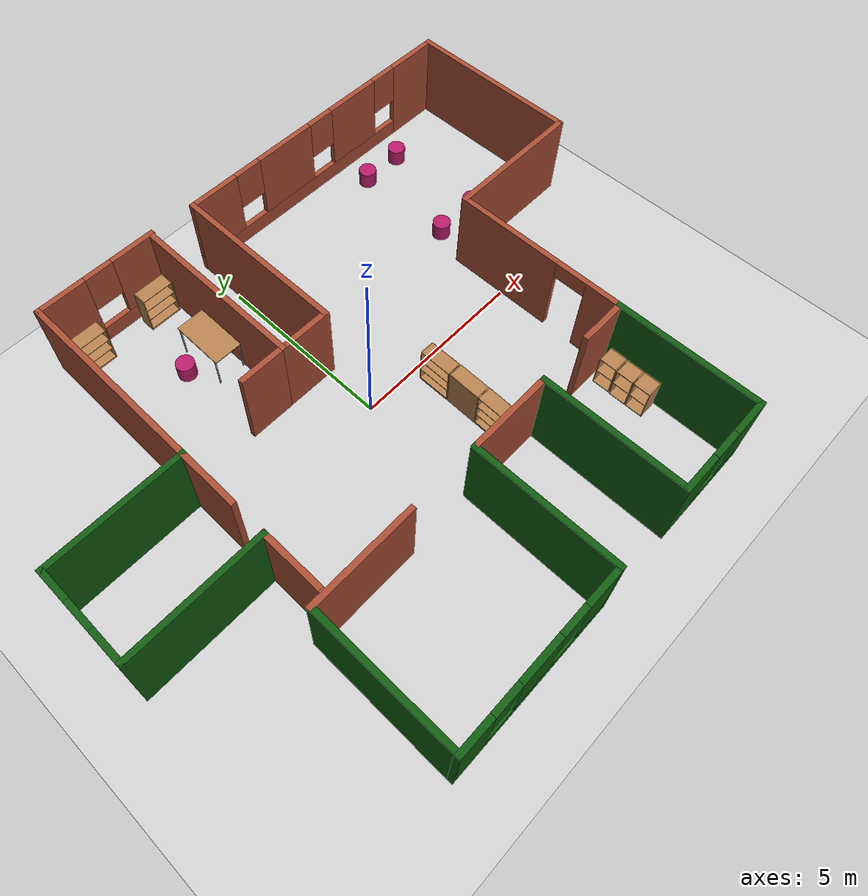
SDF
<sdf version="1.6">
 <world name="default">
  <plugin name="welcome" filename="libwelcome.so"/>
  <light name="sun" type="directional">
   <pose>0 0 10 0 -0 0</pose>
   <diffuse>0.8 0.8 0.8 1</diffuse>
   <specular>0.2 0.2 0.2 1</specular>
   <attenuation>
    <range>1000</range>
    <constant>0.9</constant>
    <linear>0.01</linear>
    <quadratic>0.001</quadratic>
   </attenuation>
   <direction>-0.5 0.1 -0.9</direction>
  </light>
  <model name="ground_plane">
   <static>1</static>
   <link name="link">
    <collision name="collision">
     <geometry><plane><normal>0 0 1</normal><size>100 100</size></plane></geometry>
     <surface>
      <contact><collide_bitmask>65535</collide_bitmask></contact>
      <friction><ode><mu>100</mu><mu2>50</mu2></ode></friction>
     </surface>
    </collision>
    <visual name="visual">
     <cast_shadows>0</cast_shadows>
     <geometry><plane><normal>0 0 1</normal><size>100 100</size></plane></geometry>
     <material>
      <script><uri>file://media/materials/scripts/gazebo.material</uri><name>Gazebo/Grey</name></script>
     </material>
    </visual>
   </link>
  </model>
  <gravity>0 0 -9.8</gravity>
  <magnetic_field>6e-06 2.3e-05 -4.2e-05</magnetic_field>
  <atmosphere type="adiabatic"/>
  <physics name="default_physics" default="0" type="ode">
   <max_step_size>0.001</max_step_size>
   <real_time_factor>1</real_time_factor>
   <real_time_update_rate>1000</real_time_update_rate>
  </physics>
  <scene><ambient>0.4 0.4 0.4 1</ambient><background>0.7 0.7 0.7 1</background><shadows>1</shadows></scene>
  <audio><device>default</device></audio>
  <spherical_coordinates>
   <surface_model>EARTH_WGS84</surface_model>
   <latitude_deg>0</latitude_deg>
   <longitude_deg>0</longitude_deg>
   <elevation>0</elevation>
   <heading_deg>0</heading_deg>
  </spherical_coordinates>
  <model name="apartment">
   <link name="Wall_0">
    <pose>-2.91418 -6.79442 0 0 -0 0</pose>
    <visual name="Wall_0_Visual_0">
     <pose>-1.99956 0 1.25 0 -0 0</pose>
     <geometry><box><size>1.00087 0.15 2.5</size></box></geometry>
     <material>
      <script><uri>file://media/materials/scripts/gazebo.material</uri><name>Gazebo/Grey</name></script>
      <ambient>0.0627451 0.352941 0.0627451 1</ambient>
     </material>
     <meta><layer>0</layer></meta>
    </visual>
    <visual name="Wall_0_Visual_1">
     <pose>0.500436 0 0.25 0 -0 0</pose>
     <geometry><box><size>3.99913 0.15 0.5</size></box></geometry>
     <material>
      <script><uri>file://media/materials/scripts/gazebo.material</uri><name>Gazebo/Grey</name></script>
      <ambient>0.0627451 0.352941 0.0627451 1</ambient>
     </material>
     <meta><layer>0</layer></meta>
    </visual>
    <visual name="Wall_0_Visual_2">
     <pose>-0.080142 0 1.5 0 -0 0</pose>
     <geometry><box><size>1.23797 0.15 2</size></box></geometry>
     <material>
      <script><uri>file://media/materials/scripts/gazebo.material</uri><name>Gazebo/Grey</name></script>
      <ambient>0.0627451 0.352941 0.0627451 1</ambient>
     </material>
     <meta><layer>0</layer></meta>
    </visual>
    <visual name="Wall_0_Visual_3">
     <pose>1.91942 0 1.5 0 -0 0</pose>
     <geometry><box><size>1.16116 0.15 2</size></box></geometry>
     <material>
      <script><uri>file://media/materials/scripts/gazebo.material</uri><name>Gazebo/Grey</name></script>
      <ambient>0.0627451 0.352941 0.0627451 1</ambient>
     </material>
     <meta><layer>0</layer></meta>
    </visual>
    <visual name="Wall_0_Visual_4">
     <pose>-1.09913 0 1.9 0 -0 0</pose>
     <geometry><box><size>0.8 0.15 1.2</size></box></geometry>
     <material>
      <script><uri>file://media/materials/scripts/gazebo.material</uri><name>Gazebo/Grey</name></script>
      <ambient>0.0627451 0.352941 0.0627451 1</ambient>
     </material>
     <meta><layer>0</layer></meta>
    </visual>
    <visual name="Wall_0_Visual_5">
     <pose>0.938844 0 1.9 0 -0 0</pose>
     <geometry><box><size>0.8 0.15 1.2</size></box></geometry>
     <material>
      <script><uri>file://media/materials/scripts/gazebo.material</uri><name>Gazebo/Grey</name></script>
      <ambient>0.0627451 0.352941 0.0627451 1</ambient>
     </material>
     <meta><layer>0</layer></meta>
    </visual>
    <collision name="Wall_0_Collision_0">
     <pose>-1.99956 0 1.25 0 -0 0</pose>
     <geometry><box><size>1.00087 0.15 2.5</size></box></geometry>
     <surface>
      <friction>
       <ode><mu>1</mu><mu2>1</mu2><fdir1>0 0 0</fdir1><slip1>0</slip1><slip2>0</slip2></ode>
       <torsional>
        <coefficient>1</coefficient>
        <patch_radius>0</patch_radius>
        <surface_radius>0</surface_radius>
        <use_patch_radius>1</use_patch_radius>
        <ode><slip>0</slip></ode>
       </torsional>
      </friction>
      <bounce><restitution_coefficient>0</restitution_coefficient><threshold>1e+06</threshold></bounce>
      <contact>
       <collide_without_contact>0</collide_without_contact>
       <collide_without_contact_bitmask>1</collide_without_contact_bitmask>
       <collide_bitmask>1</collide_bitmask>
       <ode>
        <soft_cfm>0</soft_cfm>
        <soft_erp>0.2</soft_erp>
        <kp>1e+13</kp>
        <kd>1</kd>
        <max_vel>0.01</max_vel>
        <min_depth>0</min_depth>
       </ode>
       <bullet>
        <split_impulse>1</split_impulse>
        <split_impulse_penetration_threshold>-0.01</split_impulse_penetration_threshold>
        <soft_cfm>0</soft_cfm>
        <soft_erp>0.2</soft_erp>
        <kp>1e+13</kp>
        <kd>1</kd>
       </bullet>
      </contact>
     </surface>
    </collision>
    <collision name="Wall_0_Collision_1">
     <pose>0.500436 0 0.25 0 -0 0</pose>
     <geometry><box><size>3.99913 0.15 0.5</size></box></geometry>
     <surface>
      <friction>
       <ode><mu>1</mu><mu2>1</mu2><fdir1>0 0 0</fdir1><slip1>0</slip1><slip2>0</slip2></ode>
       <torsional>
        <coefficient>1</coefficient>
        <patch_radius>0</patch_radius>
        <surface_radius>0</surface_radius>
        <use_patch_radius>1</use_patch_radius>
        <ode><slip>0</slip></ode>
       </torsional>
      </friction>
      <bounce><restitution_coefficient>0</restitution_coefficient><threshold>1e+06</threshold></bounce>
      <contact>
       <collide_without_contact>0</collide_without_contact>
       <collide_without_contact_bitmask>1</collide_without_contact_bitmask>
       <collide_bitmask>1</collide_bitmask>
       <ode>
        <soft_cfm>0</soft_cfm>
        <soft_erp>0.2</soft_erp>
        <kp>1e+13</kp>
        <kd>1</kd>
        <max_vel>0.01</max_vel>
        <min_depth>0</min_depth>
       </ode>
       <bullet>
        <split_impulse>1</split_impulse>
        <split_impulse_penetration_threshold>-0.01</split_impulse_penetration_threshold>
        <soft_cfm>0</soft_cfm>
        <soft_erp>0.2</soft_erp>
        <kp>1e+13</kp>
        <kd>1</kd>
       </bullet>
      </contact>
     </surface>
    </collision>
    <collision name="Wall_0_Collision_2">
     <pose>-0.080142 0 1.5 0 -0 0</pose>
     <geometry><box><size>1.23797 0.15 2</size></box></geometry>
     <surface>
      <friction>
       <ode><mu>1</mu><mu2>1</mu2><fdir1>0 0 0</fdir1><slip1>0</slip1><slip2>0</slip2></ode>
       <torsional>
        <coefficient>1</coefficient>
        <patch_radius>0</patch_radius>
        <surface_radius>0</surface_radius>
        <use_patch_radius>1</use_patch_radius>
        <ode><slip>0</slip></ode>
       </torsional>
      </friction>
      <bounce><restitution_coefficient>0</restitution_coefficient><threshold>1e+06</threshold></bounce>
      <contact>
       <collide_without_contact>0</collide_without_contact>
       <collide_without_contact_bitmask>1</collide_without_contact_bitmask>
       <collide_bitmask>1</collide_bitmask>
       <ode>
        <soft_cfm>0</soft_cfm>
        <soft_erp>0.2</soft_erp>
        <kp>1e+13</kp>
        <kd>1</kd>
        <max_vel>0.01</max_vel>
        <min_depth>0</min_depth>
       </ode>
       <bullet>
        <split_impulse>1</split_impulse>
        <split_impulse_penetration_threshold>-0.01</split_impulse_penetration_threshold>
        <soft_cfm>0</soft_cfm>
        <soft_erp>0.2</soft_erp>
        <kp>1e+13</kp>
        <kd>1</kd>
       </bullet>
      </contact>
     </surface>
    </collision>
    <collision name="Wall_0_Collision_3">
     <pose>1.91942 0 1.5 0 -0 0</pose>
     <geometry><box><size>1.16116 0.15 2</size></box></geometry>
     <surface>
      <friction>
       <ode><mu>1</mu><mu2>1</mu2><fdir1>0 0 0</fdir1><slip1>0</slip1><slip2>0</slip2></ode>
       <torsional>
        <coefficient>1</coefficient>
        <patch_radius>0</patch_radius>
        <surface_radius>0</surface_radius>
        <use_patch_radius>1</use_patch_radius>
        <ode><slip>0</slip></ode>
       </torsional>
      </friction>
      <bounce><restitution_coefficient>0</restitution_coefficient><threshold>1e+06</threshold></bounce>
      <contact>
       <collide_without_contact>0</collide_without_contact>
       <collide_without_contact_bitmask>1</collide_without_contact_bitmask>
       <collide_bitmask>1</collide_bitmask>
       <ode>
        <soft_cfm>0</soft_cfm>
        <soft_erp>0.2</soft_erp>
        <kp>1e+13</kp>
        <kd>1</kd>
        <max_vel>0.01</max_vel>
        <min_depth>0</min_depth>
       </ode>
       <bullet>
        <split_impulse>1</split_impulse>
        <split_impulse_penetration_threshold>-0.01</split_impulse_penetration_threshold>
        <soft_cfm>0</soft_cfm>
        <soft_erp>0.2</soft_erp>
        <kp>1e+13</kp>
        <kd>1</kd>
       </bullet>
      </contact>
     </surface>
    </collision>
    <collision name="Wall_0_Collision_4">
     <pose>-1.09913 0 1.9 0 -0 0</pose>
     <geometry><box><size>0.8 0.15 1.2</size></box></geometry>
     <surface>
      <friction>
       <ode><mu>1</mu><mu2>1</mu2><fdir1>0 0 0</fdir1><slip1>0</slip1><slip2>0</slip2></ode>
       <torsional>
        <coefficient>1</coefficient>
        <patch_radius>0</patch_radius>
        <surface_radius>0</surface_radius>
        <use_patch_radius>1</use_patch_radius>
        <ode><slip>0</slip></ode>
       </torsional>
      </friction>
      <bounce><restitution_coefficient>0</restitution_coefficient><threshold>1e+06</threshold></bounce>
      <contact>
       <collide_without_contact>0</collide_without_contact>
       <collide_without_contact_bitmask>1</collide_without_contact_bitmask>
       <collide_bitmask>1</collide_bitmask>
       <ode>
        <soft_cfm>0</soft_cfm>
        <soft_erp>0.2</soft_erp>
        <kp>1e+13</kp>
        <kd>1</kd>
        <max_vel>0.01</max_vel>
        <min_depth>0</min_depth>
       </ode>
       <bullet>
        <split_impulse>1</split_impulse>
        <split_impulse_penetration_threshold>-0.01</split_impulse_penetration_threshold>
        <soft_cfm>0</soft_cfm>
        <soft_erp>0.2</soft_erp>
        <kp>1e+13</kp>
        <kd>1</kd>
       </bullet>
      </contact>
     </surface>
    </collision>
    <collision name="Wall_0_Collision_5">
     <pose>0.938844 0 1.9 0 -0 0</pose>
     <geometry><box><size>0.8 0.15 1.2</size></box></geometry>
     <surface>
      <friction>
       <ode><mu>1</mu><mu2>1</mu2><fdir1>0 0 0</fdir1><slip1>0</slip1><slip2>0</slip2></ode>
       <torsional>
        <coefficient>1</coefficient>
        <patch_radius>0</patch_radius>
        <surface_radius>0</surface_radius>
        <use_patch_radius>1</use_patch_radius>
        <ode><slip>0</slip></ode>
       </torsional>
      </friction>
      <bounce><restitution_coefficient>0</restitution_coefficient><threshold>1e+06</threshold></bounce>
      <contact>
       <collide_without_contact>0</collide_without_contact>
       <collide_without_contact_bitmask>1</collide_without_contact_bitmask>
       <collide_bitmask>1</collide_bitmask>
       <ode>
        <soft_cfm>0</soft_cfm>
        <soft_erp>0.2</soft_erp>
        <kp>1e+13</kp>
        <kd>1</kd>
        <max_vel>0.01</max_vel>
        <min_depth>0</min_depth>
       </ode>
       <bullet>
        <split_impulse>1</split_impulse>
        <split_impulse_penetration_threshold>-0.01</split_impulse_penetration_threshold>
        <soft_cfm>0</soft_cfm>
        <soft_erp>0.2</soft_erp>
        <kp>1e+13</kp>
        <kd>1</kd>
       </bullet>
      </contact>
     </surface>
    </collision>
   </link>
   <link name="Wall_1">
    <pose>-0.489182 -4.86942 0 0 -0 1.5708</pose>
    <visual name="Wall_1_Visual">
     <pose>0 0 1.25 0 -0 0</pose>
     <geometry><box><size>4 0.15 2.5</size></box></geometry>
     <material>
      <script><uri>file://media/materials/scripts/gazebo.material</uri><name>Gazebo/Grey</name></script>
      <ambient>0.0627451 0.352941 0.0627451 1</ambient>
     </material>
     <meta><layer>0</layer></meta>
    </visual>
    <collision name="Wall_1_Collision">
     <pose>0 0 1.25 0 -0 0</pose>
     <geometry><box><size>4 0.15 2.5</size></box></geometry>
     <surface>
      <friction>
       <ode><mu>1</mu><mu2>1</mu2><fdir1>0 0 0</fdir1><slip1>0</slip1><slip2>0</slip2></ode>
       <torsional>
        <coefficient>1</coefficient>
        <patch_radius>0</patch_radius>
        <surface_radius>0</surface_radius>
        <use_patch_radius>1</use_patch_radius>
        <ode><slip>0</slip></ode>
       </torsional>
      </friction>
      <bounce><restitution_coefficient>0</restitution_coefficient><threshold>1e+06</threshold></bounce>
      <contact>
       <collide_without_contact>0</collide_without_contact>
       <collide_without_contact_bitmask>1</collide_without_contact_bitmask>
       <collide_bitmask>1</collide_bitmask>
       <ode>
        <soft_cfm>0</soft_cfm>
        <soft_erp>0.2</soft_erp>
        <kp>1e+13</kp>
        <kd>1</kd>
        <max_vel>0.01</max_vel>
        <min_depth>0</min_depth>
       </ode>
       <bullet>
        <split_impulse>1</split_impulse>
        <split_impulse_penetration_threshold>-0.01</split_impulse_penetration_threshold>
        <soft_cfm>0</soft_cfm>
        <soft_erp>0.2</soft_erp>
        <kp>1e+13</kp>
        <kd>1</kd>
       </bullet>
      </contact>
     </surface>
    </collision>
   </link>
   <link name="Wall_13">
    <pose>4.71082 -0.519415 0 0 -0 1.5708</pose>
    <visual name="Wall_13_Visual_0">
     <pose>-1.98617 0 1.25 0 -0 0</pose>
     <geometry><box><size>1.02765 0.15 2.5</size></box></geometry>
     <material>
      <script><uri>file://media/materials/scripts/gazebo.material</uri><name>Gazebo/Bricks</name></script>
      <ambient>1 1 1 1</ambient>
     </material>
     <meta><layer>0</layer></meta>
    </visual>
    <visual name="Wall_13_Visual_1">
     <pose>0.963826 0 1.25 0 -0 0</pose>
     <geometry><box><size>3.07235 0.15 2.5</size></box></geometry>
     <material>
      <script><uri>file://media/materials/scripts/gazebo.material</uri><name>Gazebo/Bricks</name></script>
      <ambient>1 1 1 1</ambient>
     </material>
     <meta><layer>0</layer></meta>
    </visual>
    <visual name="Wall_13_Visual_2">
     <pose>-1.02235 0 2.25 0 -0 0</pose>
     <geometry><box><size>0.9 0.15 0.5</size></box></geometry>
     <material>
      <script><uri>file://media/materials/scripts/gazebo.material</uri><name>Gazebo/Bricks</name></script>
      <ambient>1 1 1 1</ambient>
     </material>
     <meta><layer>0</layer></meta>
    </visual>
    <collision name="Wall_13_Collision_0">
     <pose>-1.98617 0 1.25 0 -0 0</pose>
     <geometry><box><size>1.02765 0.15 2.5</size></box></geometry>
     <surface>
      <friction>
       <ode><mu>1</mu><mu2>1</mu2><fdir1>0 0 0</fdir1><slip1>0</slip1><slip2>0</slip2></ode>
       <torsional>
        <coefficient>1</coefficient>
        <patch_radius>0</patch_radius>
        <surface_radius>0</surface_radius>
        <use_patch_radius>1</use_patch_radius>
        <ode><slip>0</slip></ode>
       </torsional>
      </friction>
      <bounce><restitution_coefficient>0</restitution_coefficient><threshold>1e+06</threshold></bounce>
      <contact>
       <collide_without_contact>0</collide_without_contact>
       <collide_without_contact_bitmask>1</collide_without_contact_bitmask>
       <collide_bitmask>1</collide_bitmask>
       <ode>
        <soft_cfm>0</soft_cfm>
        <soft_erp>0.2</soft_erp>
        <kp>1e+13</kp>
        <kd>1</kd>
        <max_vel>0.01</max_vel>
        <min_depth>0</min_depth>
       </ode>
       <bullet>
        <split_impulse>1</split_impulse>
        <split_impulse_penetration_threshold>-0.01</split_impulse_penetration_threshold>
        <soft_cfm>0</soft_cfm>
        <soft_erp>0.2</soft_erp>
        <kp>1e+13</kp>
        <kd>1</kd>
       </bullet>
      </contact>
     </surface>
    </collision>
    <collision name="Wall_13_Collision_1">
     <pose>0.963826 0 1.25 0 -0 0</pose>
     <geometry><box><size>3.07235 0.15 2.5</size></box></geometry>
     <surface>
      <friction>
       <ode><mu>1</mu><mu2>1</mu2><fdir1>0 0 0</fdir1><slip1>0</slip1><slip2>0</slip2></ode>
       <torsional>
        <coefficient>1</coefficient>
        <patch_radius>0</patch_radius>
        <surface_radius>0</surface_radius>
        <use_patch_radius>1</use_patch_radius>
        <ode><slip>0</slip></ode>
       </torsional>
      </friction>
      <bounce><restitution_coefficient>0</restitution_coefficient><threshold>1e+06</threshold></bounce>
      <contact>
       <collide_without_contact>0</collide_without_contact>
       <collide_without_contact_bitmask>1</collide_without_contact_bitmask>
       <collide_bitmask>1</collide_bitmask>
       <ode>
        <soft_cfm>0</soft_cfm>
        <soft_erp>0.2</soft_erp>
        <kp>1e+13</kp>
        <kd>1</kd>
        <max_vel>0.01</max_vel>
        <min_depth>0</min_depth>
       </ode>
       <bullet>
        <split_impulse>1</split_impulse>
        <split_impulse_penetration_threshold>-0.01</split_impulse_penetration_threshold>
        <soft_cfm>0</soft_cfm>
        <soft_erp>0.2</soft_erp>
        <kp>1e+13</kp>
        <kd>1</kd>
       </bullet>
      </contact>
     </surface>
    </collision>
    <collision name="Wall_13_Collision_2">
     <pose>-1.02235 0 2.25 0 -0 0</pose>
     <geometry><box><size>0.9 0.15 0.5</size></box></geometry>
     <surface>
      <friction>
       <ode><mu>1</mu><mu2>1</mu2><fdir1>0 0 0</fdir1><slip1>0</slip1><slip2>0</slip2></ode>
       <torsional>
        <coefficient>1</coefficient>
        <patch_radius>0</patch_radius>
        <surface_radius>0</surface_radius>
        <use_patch_radius>1</use_patch_radius>
        <ode><slip>0</slip></ode>
       </torsional>
      </friction>
      <bounce><restitution_coefficient>0</restitution_coefficient><threshold>1e+06</threshold></bounce>
      <contact>
       <collide_without_contact>0</collide_without_contact>
       <collide_without_contact_bitmask>1</collide_without_contact_bitmask>
       <collide_bitmask>1</collide_bitmask>
       <ode>
        <soft_cfm>0</soft_cfm>
        <soft_erp>0.2</soft_erp>
        <kp>1e+13</kp>
        <kd>1</kd>
        <max_vel>0.01</max_vel>
        <min_depth>0</min_depth>
       </ode>
       <bullet>
        <split_impulse>1</split_impulse>
        <split_impulse_penetration_threshold>-0.01</split_impulse_penetration_threshold>
        <soft_cfm>0</soft_cfm>
        <soft_erp>0.2</soft_erp>
        <kp>1e+13</kp>
        <kd>1</kd>
       </bullet>
      </contact>
     </surface>
    </collision>
   </link>
   <link name="Wall_14">
    <pose>6.63582 1.90558 0 0 -0 0</pose>
    <visual name="Wall_14_Visual">
     <pose>0 0 1.25 0 -0 0</pose>
     <geometry><box><size>4 0.15 2.5</size></box></geometry>
     <material>
      <script><uri>file://media/materials/scripts/gazebo.material</uri><name>Gazebo/Bricks</name></script>
      <ambient>1 1 1 1</ambient>
     </material>
     <meta><layer>0</layer></meta>
    </visual>
    <collision name="Wall_14_Collision">
     <pose>0 0 1.25 0 -0 0</pose>
     <geometry><box><size>4 0.15 2.5</size></box></geometry>
     <surface>
      <friction>
       <ode><mu>1</mu><mu2>1</mu2><fdir1>0 0 0</fdir1><slip1>0</slip1><slip2>0</slip2></ode>
       <torsional>
        <coefficient>1</coefficient>
        <patch_radius>0</patch_radius>
        <surface_radius>0</surface_radius>
        <use_patch_radius>1</use_patch_radius>
        <ode><slip>0</slip></ode>
       </torsional>
      </friction>
      <bounce><restitution_coefficient>0</restitution_coefficient><threshold>1e+06</threshold></bounce>
      <contact>
       <collide_without_contact>0</collide_without_contact>
       <collide_without_contact_bitmask>1</collide_without_contact_bitmask>
       <collide_bitmask>1</collide_bitmask>
       <ode>
        <soft_cfm>0</soft_cfm>
        <soft_erp>0.2</soft_erp>
        <kp>1e+13</kp>
        <kd>1</kd>
        <max_vel>0.01</max_vel>
        <min_depth>0</min_depth>
       </ode>
       <bullet>
        <split_impulse>1</split_impulse>
        <split_impulse_penetration_threshold>-0.01</split_impulse_penetration_threshold>
        <soft_cfm>0</soft_cfm>
        <soft_erp>0.2</soft_erp>
        <kp>1e+13</kp>
        <kd>1</kd>
       </bullet>
      </contact>
     </surface>
    </collision>
   </link>
   <link name="Wall_15">
    <pose>8.56082 4.33059 0 0 -0 1.5708</pose>
    <visual name="Wall_15_Visual">
     <pose>0 0 1.25 0 -0 0</pose>
     <geometry><box><size>5 0.15 2.5</size></box></geometry>
     <material>
      <script><uri>file://media/materials/scripts/gazebo.material</uri><name>Gazebo/Bricks</name></script>
      <ambient>1 1 1 1</ambient>
     </material>
     <meta><layer>0</layer></meta>
    </visual>
    <collision name="Wall_15_Collision">
     <pose>0 0 1.25 0 -0 0</pose>
     <geometry><box><size>5 0.15 2.5</size></box></geometry>
     <surface>
      <friction>
       <ode><mu>1</mu><mu2>1</mu2><fdir1>0 0 0</fdir1><slip1>0</slip1><slip2>0</slip2></ode>
       <torsional>
        <coefficient>1</coefficient>
        <patch_radius>0</patch_radius>
        <surface_radius>0</surface_radius>
        <use_patch_radius>1</use_patch_radius>
        <ode><slip>0</slip></ode>
       </torsional>
      </friction>
      <bounce><restitution_coefficient>0</restitution_coefficient><threshold>1e+06</threshold></bounce>
      <contact>
       <collide_without_contact>0</collide_without_contact>
       <collide_without_contact_bitmask>1</collide_without_contact_bitmask>
       <collide_bitmask>1</collide_bitmask>
       <ode>
        <soft_cfm>0</soft_cfm>
        <soft_erp>0.2</soft_erp>
        <kp>1e+13</kp>
        <kd>1</kd>
        <max_vel>0.01</max_vel>
        <min_depth>0</min_depth>
       </ode>
       <bullet>
        <split_impulse>1</split_impulse>
        <split_impulse_penetration_threshold>-0.01</split_impulse_penetration_threshold>
        <soft_cfm>0</soft_cfm>
        <soft_erp>0.2</soft_erp>
        <kp>1e+13</kp>
        <kd>1</kd>
       </bullet>
      </contact>
     </surface>
    </collision>
   </link>
   <link name="Wall_16">
    <pose>4.13582 6.75558 0 0 -0 3.14159</pose>
    <visual name="Wall_16_Visual_1">
     <pose>0.807869 0 0.25 0 -0 0</pose>
     <geometry><box><size>7.38426 0.15 0.5</size></box></geometry>
     <material>
      <script><uri>file://media/materials/scripts/gazebo.material</uri><name>Gazebo/Bricks</name></script>
      <ambient>1 1 1 1</ambient>
     </material>
     <meta><layer>0</layer></meta>
    </visual>
    <visual name="Wall_16_Visual_0">
     <pose>-3.69213 0 1.25 0 -0 0</pose>
     <geometry><box><size>1.61574 0.15 2.5</size></box></geometry>
     <material>
      <script><uri>file://media/materials/scripts/gazebo.material</uri><name>Gazebo/Bricks</name></script>
      <ambient>1 1 1 1</ambient>
     </material>
     <meta><layer>0</layer></meta>
    </visual>
    <visual name="Wall_16_Visual_2">
     <pose>-1.25235 0 1.5 0 -0 0</pose>
     <geometry><box><size>1.66382 0.15 2</size></box></geometry>
     <material>
      <script><uri>file://media/materials/scripts/gazebo.material</uri><name>Gazebo/Bricks</name></script>
      <ambient>1 1 1 1</ambient>
     </material>
     <meta><layer>0</layer></meta>
    </visual>
    <visual name="Wall_16_Visual_3">
     <pose>1.29511 0 1.5 0 -0 0</pose>
     <geometry><box><size>1.83111 0.15 2</size></box></geometry>
     <material>
      <script><uri>file://media/materials/scripts/gazebo.material</uri><name>Gazebo/Bricks</name></script>
      <ambient>1 1 1 1</ambient>
     </material>
     <meta><layer>0</layer></meta>
    </visual>
    <visual name="Wall_16_Visual_4">
     <pose>3.75534 0 1.5 0 -0 0</pose>
     <geometry><box><size>1.48933 0.15 2</size></box></geometry>
     <material>
      <script><uri>file://media/materials/scripts/gazebo.material</uri><name>Gazebo/Bricks</name></script>
      <ambient>1 1 1 1</ambient>
     </material>
     <meta><layer>0</layer></meta>
    </visual>
    <visual name="Wall_16_Visual_5">
     <pose>-2.48426 0 1.9 0 -0 0</pose>
     <geometry><box><size>0.8 0.15 1.2</size></box></geometry>
     <material>
      <script><uri>file://media/materials/scripts/gazebo.material</uri><name>Gazebo/Bricks</name></script>
      <ambient>1 1 1 1</ambient>
     </material>
     <meta><layer>0</layer></meta>
    </visual>
    <visual name="Wall_16_Visual_6">
     <pose>-0.020444 0 1.9 0 -0 0</pose>
     <geometry><box><size>0.8 0.15 1.2</size></box></geometry>
     <material>
      <script><uri>file://media/materials/scripts/gazebo.material</uri><name>Gazebo/Bricks</name></script>
      <ambient>1 1 1 1</ambient>
     </material>
     <meta><layer>0</layer></meta>
    </visual>
    <visual name="Wall_16_Visual_7">
     <pose>2.61067 0 1.9 0 -0 0</pose>
     <geometry><box><size>0.8 0.15 1.2</size></box></geometry>
     <material>
      <script><uri>file://media/materials/scripts/gazebo.material</uri><name>Gazebo/Bricks</name></script>
      <ambient>1 1 1 1</ambient>
     </material>
     <meta><layer>0</layer></meta>
    </visual>
    <collision name="Wall_16_Collision_0">
     <pose>-3.69213 0 1.25 0 -0 0</pose>
     <geometry><box><size>1.61574 0.15 2.5</size></box></geometry>
     <surface>
      <friction>
       <ode><mu>1</mu><mu2>1</mu2><fdir1>0 0 0</fdir1><slip1>0</slip1><slip2>0</slip2></ode>
       <torsional>
        <coefficient>1</coefficient>
        <patch_radius>0</patch_radius>
        <surface_radius>0</surface_radius>
        <use_patch_radius>1</use_patch_radius>
        <ode><slip>0</slip></ode>
       </torsional>
      </friction>
      <bounce><restitution_coefficient>0</restitution_coefficient><threshold>1e+06</threshold></bounce>
      <contact>
       <collide_without_contact>0</collide_without_contact>
       <collide_without_contact_bitmask>1</collide_without_contact_bitmask>
       <collide_bitmask>1</collide_bitmask>
       <ode>
        <soft_cfm>0</soft_cfm>
        <soft_erp>0.2</soft_erp>
        <kp>1e+13</kp>
        <kd>1</kd>
        <max_vel>0.01</max_vel>
        <min_depth>0</min_depth>
       </ode>
       <bullet>
        <split_impulse>1</split_impulse>
        <split_impulse_penetration_threshold>-0.01</split_impulse_penetration_threshold>
        <soft_cfm>0</soft_cfm>
        <soft_erp>0.2</soft_erp>
        <kp>1e+13</kp>
        <kd>1</kd>
       </bullet>
      </contact>
     </surface>
    </collision>
    <collision name="Wall_16_Collision_1">
     <pose>0.807869 0 0.25 0 -0 0</pose>
     <geometry><box><size>7.38426 0.15 0.5</size></box></geometry>
     <surface>
      <friction>
       <ode><mu>1</mu><mu2>1</mu2><fdir1>0 0 0</fdir1><slip1>0</slip1><slip2>0</slip2></ode>
       <torsional>
        <coefficient>1</coefficient>
        <patch_radius>0</patch_radius>
        <surface_radius>0</surface_radius>
        <use_patch_radius>1</use_patch_radius>
        <ode><slip>0</slip></ode>
       </torsional>
      </friction>
      <bounce><restitution_coefficient>0</restitution_coefficient><threshold>1e+06</threshold></bounce>
      <contact>
       <collide_without_contact>0</collide_without_contact>
       <collide_without_contact_bitmask>1</collide_without_contact_bitmask>
       <collide_bitmask>1</collide_bitmask>
       <ode>
        <soft_cfm>0</soft_cfm>
        <soft_erp>0.2</soft_erp>
        <kp>1e+13</kp>
        <kd>1</kd>
        <max_vel>0.01</max_vel>
        <min_depth>0</min_depth>
       </ode>
       <bullet>
        <split_impulse>1</split_impulse>
        <split_impulse_penetration_threshold>-0.01</split_impulse_penetration_threshold>
        <soft_cfm>0</soft_cfm>
        <soft_erp>0.2</soft_erp>
        <kp>1e+13</kp>
        <kd>1</kd>
       </bullet>
      </contact>
     </surface>
    </collision>
    <collision name="Wall_16_Collision_2">
     <pose>-1.25235 0 1.5 0 -0 0</pose>
     <geometry><box><size>1.66382 0.15 2</size></box></geometry>
     <surface>
      <friction>
       <ode><mu>1</mu><mu2>1</mu2><fdir1>0 0 0</fdir1><slip1>0</slip1><slip2>0</slip2></ode>
       <torsional>
        <coefficient>1</coefficient>
        <patch_radius>0</patch_radius>
        <surface_radius>0</surface_radius>
        <use_patch_radius>1</use_patch_radius>
        <ode><slip>0</slip></ode>
       </torsional>
      </friction>
      <bounce><restitution_coefficient>0</restitution_coefficient><threshold>1e+06</threshold></bounce>
      <contact>
       <collide_without_contact>0</collide_without_contact>
       <collide_without_contact_bitmask>1</collide_without_contact_bitmask>
       <collide_bitmask>1</collide_bitmask>
       <ode>
        <soft_cfm>0</soft_cfm>
        <soft_erp>0.2</soft_erp>
        <kp>1e+13</kp>
        <kd>1</kd>
        <max_vel>0.01</max_vel>
        <min_depth>0</min_depth>
       </ode>
       <bullet>
        <split_impulse>1</split_impulse>
        <split_impulse_penetration_threshold>-0.01</split_impulse_penetration_threshold>
        <soft_cfm>0</soft_cfm>
        <soft_erp>0.2</soft_erp>
        <kp>1e+13</kp>
        <kd>1</kd>
       </bullet>
      </contact>
     </surface>
    </collision>
    <collision name="Wall_16_Collision_3">
     <pose>1.29511 0 1.5 0 -0 0</pose>
     <geometry><box><size>1.83111 0.15 2</size></box></geometry>
     <surface>
      <friction>
       <ode><mu>1</mu><mu2>1</mu2><fdir1>0 0 0</fdir1><slip1>0</slip1><slip2>0</slip2></ode>
       <torsional>
        <coefficient>1</coefficient>
        <patch_radius>0</patch_radius>
        <surface_radius>0</surface_radius>
        <use_patch_radius>1</use_patch_radius>
        <ode><slip>0</slip></ode>
       </torsional>
      </friction>
      <bounce><restitution_coefficient>0</restitution_coefficient><threshold>1e+06</threshold></bounce>
      <contact>
       <collide_without_contact>0</collide_without_contact>
       <collide_without_contact_bitmask>1</collide_without_contact_bitmask>
       <collide_bitmask>1</collide_bitmask>
       <ode>
        <soft_cfm>0</soft_cfm>
        <soft_erp>0.2</soft_erp>
        <kp>1e+13</kp>
        <kd>1</kd>
        <max_vel>0.01</max_vel>
        <min_depth>0</min_depth>
       </ode>
       <bullet>
        <split_impulse>1</split_impulse>
        <split_impulse_penetration_threshold>-0.01</split_impulse_penetration_threshold>
        <soft_cfm>0</soft_cfm>
        <soft_erp>0.2</soft_erp>
        <kp>1e+13</kp>
        <kd>1</kd>
       </bullet>
      </contact>
     </surface>
    </collision>
    <collision name="Wall_16_Collision_4">
     <pose>3.75534 0 1.5 0 -0 0</pose>
     <geometry><box><size>1.48933 0.15 2</size></box></geometry>
     <surface>
      <friction>
       <ode><mu>1</mu><mu2>1</mu2><fdir1>0 0 0</fdir1><slip1>0</slip1><slip2>0</slip2></ode>
       <torsional>
        <coefficient>1</coefficient>
        <patch_radius>0</patch_radius>
        <surface_radius>0</surface_radius>
        <use_patch_radius>1</use_patch_radius>
        <ode><slip>0</slip></ode>
       </torsional>
      </friction>
      <bounce><restitution_coefficient>0</restitution_coefficient><threshold>1e+06</threshold></bounce>
      <contact>
       <collide_without_contact>0</collide_without_contact>
       <collide_without_contact_bitmask>1</collide_without_contact_bitmask>
       <collide_bitmask>1</collide_bitmask>
       <ode>
        <soft_cfm>0</soft_cfm>
        <soft_erp>0.2</soft_erp>
        <kp>1e+13</kp>
        <kd>1</kd>
        <max_vel>0.01</max_vel>
        <min_depth>0</min_depth>
       </ode>
       <bullet>
        <split_impulse>1</split_impulse>
        <split_impulse_penetration_threshold>-0.01</split_impulse_penetration_threshold>
        <soft_cfm>0</soft_cfm>
        <soft_erp>0.2</soft_erp>
        <kp>1e+13</kp>
        <kd>1</kd>
       </bullet>
      </contact>
     </surface>
    </collision>
    <collision name="Wall_16_Collision_5">
     <pose>-2.48426 0 1.9 0 -0 0</pose>
     <geometry><box><size>0.8 0.15 1.2</size></box></geometry>
     <surface>
      <friction>
       <ode><mu>1</mu><mu2>1</mu2><fdir1>0 0 0</fdir1><slip1>0</slip1><slip2>0</slip2></ode>
       <torsional>
        <coefficient>1</coefficient>
        <patch_radius>0</patch_radius>
        <surface_radius>0</surface_radius>
        <use_patch_radius>1</use_patch_radius>
        <ode><slip>0</slip></ode>
       </torsional>
      </friction>
      <bounce><restitution_coefficient>0</restitution_coefficient><threshold>1e+06</threshold></bounce>
      <contact>
       <collide_without_contact>0</collide_without_contact>
       <collide_without_contact_bitmask>1</collide_without_contact_bitmask>
       <collide_bitmask>1</collide_bitmask>
       <ode>
        <soft_cfm>0</soft_cfm>
        <soft_erp>0.2</soft_erp>
        <kp>1e+13</kp>
        <kd>1</kd>
        <max_vel>0.01</max_vel>
        <min_depth>0</min_depth>
       </ode>
       <bullet>
        <split_impulse>1</split_impulse>
        <split_impulse_penetration_threshold>-0.01</split_impulse_penetration_threshold>
        <soft_cfm>0</soft_cfm>
        <soft_erp>0.2</soft_erp>
        <kp>1e+13</kp>
        <kd>1</kd>
       </bullet>
      </contact>
     </surface>
    </collision>
    <collision name="Wall_16_Collision_6">
     <pose>-0.020444 0 1.9 0 -0 0</pose>
     <geometry><box><size>0.8 0.15 1.2</size></box></geometry>
     <surface>
      <friction>
       <ode><mu>1</mu><mu2>1</mu2><fdir1>0 0 0</fdir1><slip1>0</slip1><slip2>0</slip2></ode>
       <torsional>
        <coefficient>1</coefficient>
        <patch_radius>0</patch_radius>
        <surface_radius>0</surface_radius>
        <use_patch_radius>1</use_patch_radius>
        <ode><slip>0</slip></ode>
       </torsional>
      </friction>
      <bounce><restitution_coefficient>0</restitution_coefficient><threshold>1e+06</threshold></bounce>
      <contact>
       <collide_without_contact>0</collide_without_contact>
       <collide_without_contact_bitmask>1</collide_without_contact_bitmask>
       <collide_bitmask>1</collide_bitmask>
       <ode>
        <soft_cfm>0</soft_cfm>
        <soft_erp>0.2</soft_erp>
        <kp>1e+13</kp>
        <kd>1</kd>
        <max_vel>0.01</max_vel>
        <min_depth>0</min_depth>
       </ode>
       <bullet>
        <split_impulse>1</split_impulse>
        <split_impulse_penetration_threshold>-0.01</split_impulse_penetration_threshold>
        <soft_cfm>0</soft_cfm>
        <soft_erp>0.2</soft_erp>
        <kp>1e+13</kp>
        <kd>1</kd>
       </bullet>
      </contact>
     </surface>
    </collision>
    <collision name="Wall_16_Collision_7">
     <pose>2.61067 0 1.9 0 -0 0</pose>
     <geometry><box><size>0.8 0.15 1.2</size></box></geometry>
     <surface>
      <friction>
       <ode><mu>1</mu><mu2>1</mu2><fdir1>0 0 0</fdir1><slip1>0</slip1><slip2>0</slip2></ode>
       <torsional>
        <coefficient>1</coefficient>
        <patch_radius>0</patch_radius>
        <surface_radius>0</surface_radius>
        <use_patch_radius>1</use_patch_radius>
        <ode><slip>0</slip></ode>
       </torsional>
      </friction>
      <bounce><restitution_coefficient>0</restitution_coefficient><threshold>1e+06</threshold></bounce>
      <contact>
       <collide_without_contact>0</collide_without_contact>
       <collide_without_contact_bitmask>1</collide_without_contact_bitmask>
       <collide_bitmask>1</collide_bitmask>
       <ode>
        <soft_cfm>0</soft_cfm>
        <soft_erp>0.2</soft_erp>
        <kp>1e+13</kp>
        <kd>1</kd>
        <max_vel>0.01</max_vel>
        <min_depth>0</min_depth>
       </ode>
       <bullet>
        <split_impulse>1</split_impulse>
        <split_impulse_penetration_threshold>-0.01</split_impulse_penetration_threshold>
        <soft_cfm>0</soft_cfm>
        <soft_erp>0.2</soft_erp>
        <kp>1e+13</kp>
        <kd>1</kd>
       </bullet>
      </contact>
     </surface>
    </collision>
   </link>
   <link name="Wall_17">
    <pose>-0.289182 4.33059 0 0 0 -1.5708</pose>
    <visual name="Wall_17_Visual">
     <pose>0 0 1.25 0 -0 0</pose>
     <geometry><box><size>5 0.15 2.5</size></box></geometry>
     <material>
      <script><uri>file://media/materials/scripts/gazebo.material</uri><name>Gazebo/Bricks</name></script>
      <ambient>1 1 1 1</ambient>
     </material>
     <meta><layer>0</layer></meta>
    </visual>
    <collision name="Wall_17_Collision">
     <pose>0 0 1.25 0 -0 0</pose>
     <geometry><box><size>5 0.15 2.5</size></box></geometry>
     <surface>
      <friction>
       <ode><mu>1</mu><mu2>1</mu2><fdir1>0 0 0</fdir1><slip1>0</slip1><slip2>0</slip2></ode>
       <torsional>
        <coefficient>1</coefficient>
        <patch_radius>0</patch_radius>
        <surface_radius>0</surface_radius>
        <use_patch_radius>1</use_patch_radius>
        <ode><slip>0</slip></ode>
       </torsional>
      </friction>
      <bounce><restitution_coefficient>0</restitution_coefficient><threshold>1e+06</threshold></bounce>
      <contact>
       <collide_without_contact>0</collide_without_contact>
       <collide_without_contact_bitmask>1</collide_without_contact_bitmask>
       <collide_bitmask>1</collide_bitmask>
       <ode>
        <soft_cfm>0</soft_cfm>
        <soft_erp>0.2</soft_erp>
        <kp>1e+13</kp>
        <kd>1</kd>
        <max_vel>0.01</max_vel>
        <min_depth>0</min_depth>
       </ode>
       <bullet>
        <split_impulse>1</split_impulse>
        <split_impulse_penetration_threshold>-0.01</split_impulse_penetration_threshold>
        <soft_cfm>0</soft_cfm>
        <soft_erp>0.2</soft_erp>
        <kp>1e+13</kp>
        <kd>1</kd>
       </bullet>
      </contact>
     </surface>
    </collision>
   </link>
   <link name="Wall_18">
    <pose>-0.964182 1.90558 0 0 -0 3.14159</pose>
    <visual name="Wall_18_Visual">
     <pose>0 0 1.25 0 -0 0</pose>
     <geometry><box><size>1.5 0.15 2.5</size></box></geometry>
     <material>
      <script><uri>file://media/materials/scripts/gazebo.material</uri><name>Gazebo/Bricks</name></script>
      <ambient>1 1 1 1</ambient>
     </material>
     <meta><layer>0</layer></meta>
    </visual>
    <collision name="Wall_18_Collision">
     <pose>0 0 1.25 0 -0 0</pose>
     <geometry><box><size>1.5 0.15 2.5</size></box></geometry>
     <surface>
      <friction>
       <ode><mu>1</mu><mu2>1</mu2><fdir1>0 0 0</fdir1><slip1>0</slip1><slip2>0</slip2></ode>
       <torsional>
        <coefficient>1</coefficient>
        <patch_radius>0</patch_radius>
        <surface_radius>0</surface_radius>
        <use_patch_radius>1</use_patch_radius>
        <ode><slip>0</slip></ode>
       </torsional>
      </friction>
      <bounce><restitution_coefficient>0</restitution_coefficient><threshold>1e+06</threshold></bounce>
      <contact>
       <collide_without_contact>0</collide_without_contact>
       <collide_without_contact_bitmask>1</collide_without_contact_bitmask>
       <collide_bitmask>1</collide_bitmask>
       <ode>
        <soft_cfm>0</soft_cfm>
        <soft_erp>0.2</soft_erp>
        <kp>1e+13</kp>
        <kd>1</kd>
        <max_vel>0.01</max_vel>
        <min_depth>0</min_depth>
       </ode>
       <bullet>
        <split_impulse>1</split_impulse>
        <split_impulse_penetration_threshold>-0.01</split_impulse_penetration_threshold>
        <soft_cfm>0</soft_cfm>
        <soft_erp>0.2</soft_erp>
        <kp>1e+13</kp>
        <kd>1</kd>
       </bullet>
      </contact>
     </surface>
    </collision>
   </link>
   <link name="Wall_2">
    <pose>0.685818 -2.94442 0 0 -0 0</pose>
    <visual name="Wall_2_Visual">
     <pose>0 0 1.25 0 -0 0</pose>
     <geometry><box><size>2.5 0.15 2.5</size></box></geometry>
     <material>
      <script><uri>file://media/materials/scripts/gazebo.material</uri><name>Gazebo/Bricks</name></script>
      <ambient>1 1 1 1</ambient>
     </material>
     <meta><layer>0</layer></meta>
    </visual>
    <collision name="Wall_2_Collision">
     <pose>0 0 1.25 0 -0 0</pose>
     <geometry><box><size>2.5 0.15 2.5</size></box></geometry>
     <surface>
      <friction>
       <ode><mu>1</mu><mu2>1</mu2><fdir1>0 0 0</fdir1><slip1>0</slip1><slip2>0</slip2></ode>
       <torsional>
        <coefficient>1</coefficient>
        <patch_radius>0</patch_radius>
        <surface_radius>0</surface_radius>
        <use_patch_radius>1</use_patch_radius>
        <ode><slip>0</slip></ode>
       </torsional>
      </friction>
      <bounce><restitution_coefficient>0</restitution_coefficient><threshold>1e+06</threshold></bounce>
      <contact>
       <collide_without_contact>0</collide_without_contact>
       <collide_without_contact_bitmask>1</collide_without_contact_bitmask>
       <collide_bitmask>1</collide_bitmask>
       <ode>
        <soft_cfm>0</soft_cfm>
        <soft_erp>0.2</soft_erp>
        <kp>1e+13</kp>
        <kd>1</kd>
        <max_vel>0.01</max_vel>
        <min_depth>0</min_depth>
       </ode>
       <bullet>
        <split_impulse>1</split_impulse>
        <split_impulse_penetration_threshold>-0.01</split_impulse_penetration_threshold>
        <soft_cfm>0</soft_cfm>
        <soft_erp>0.2</soft_erp>
        <kp>1e+13</kp>
        <kd>1</kd>
       </bullet>
      </contact>
     </surface>
    </collision>
   </link>
   <link name="Wall_20">
    <pose>-1.63918 4.33059 0 0 -0 1.5708</pose>
    <visual name="Wall_20_Visual">
     <pose>0 0 1.25 0 -0 0</pose>
     <geometry><box><size>5 0.15 2.5</size></box></geometry>
     <material>
      <script><uri>file://media/materials/scripts/gazebo.material</uri><name>Gazebo/Bricks</name></script>
      <ambient>1 1 1 1</ambient>
     </material>
     <meta><layer>0</layer></meta>
    </visual>
    <collision name="Wall_20_Collision">
     <pose>0 0 1.25 0 -0 0</pose>
     <geometry><box><size>5 0.15 2.5</size></box></geometry>
     <surface>
      <friction>
       <ode><mu>1</mu><mu2>1</mu2><fdir1>0 0 0</fdir1><slip1>0</slip1><slip2>0</slip2></ode>
       <torsional>
        <coefficient>1</coefficient>
        <patch_radius>0</patch_radius>
        <surface_radius>0</surface_radius>
        <use_patch_radius>1</use_patch_radius>
        <ode><slip>0</slip></ode>
       </torsional>
      </friction>
      <bounce><restitution_coefficient>0</restitution_coefficient><threshold>1e+06</threshold></bounce>
      <contact>
       <collide_without_contact>0</collide_without_contact>
       <collide_without_contact_bitmask>1</collide_without_contact_bitmask>
       <collide_bitmask>1</collide_bitmask>
       <ode>
        <soft_cfm>0</soft_cfm>
        <soft_erp>0.2</soft_erp>
        <kp>1e+13</kp>
        <kd>1</kd>
        <max_vel>0.01</max_vel>
        <min_depth>0</min_depth>
       </ode>
       <bullet>
        <split_impulse>1</split_impulse>
        <split_impulse_penetration_threshold>-0.01</split_impulse_penetration_threshold>
        <soft_cfm>0</soft_cfm>
        <soft_erp>0.2</soft_erp>
        <kp>1e+13</kp>
        <kd>1</kd>
       </bullet>
      </contact>
     </surface>
    </collision>
   </link>
   <link name="Wall_26">
    <pose>-8.56082 0.144415 0 0 0 -1.5708</pose>
    <visual name="Wall_26_Visual_0">
     <pose>-0.908752 0 1.25 0 -0 0</pose>
     <geometry><box><size>0.932496 0.15 2.5</size></box></geometry>
     <material>
      <script><uri>file://media/materials/scripts/gazebo.material</uri><name>Gazebo/Grey</name></script>
      <ambient>0.0627451 0.345098 0.0627451 1</ambient>
     </material>
     <meta><layer>0</layer></meta>
    </visual>
    <visual name="Wall_26_Visual_1">
     <pose>0.466248 0 0.25 0 -0 0</pose>
     <geometry><box><size>1.8175 0.15 0.5</size></box></geometry>
     <material>
      <script><uri>file://media/materials/scripts/gazebo.material</uri><name>Gazebo/Grey</name></script>
      <ambient>0.0627451 0.345098 0.0627451 1</ambient>
     </material>
     <meta><layer>0</layer></meta>
    </visual>
    <visual name="Wall_26_Visual_2">
     <pose>0.866248 0 1.5 0 -0 0</pose>
     <geometry><box><size>1.0175 0.15 2</size></box></geometry>
     <material>
      <script><uri>file://media/materials/scripts/gazebo.material</uri><name>Gazebo/Grey</name></script>
      <ambient>0.0627451 0.345098 0.0627451 1</ambient>
     </material>
     <meta><layer>0</layer></meta>
    </visual>
    <visual name="Wall_26_Visual_3">
     <pose>-0.042504 0 1.9 0 -0 0</pose>
     <geometry><box><size>0.8 0.15 1.2</size></box></geometry>
     <material>
      <script><uri>file://media/materials/scripts/gazebo.material</uri><name>Gazebo/Grey</name></script>
      <ambient>0.0627451 0.345098 0.0627451 1</ambient>
     </material>
     <meta><layer>0</layer></meta>
    </visual>
    <collision name="Wall_26_Collision_0">
     <pose>-0.908752 0 1.25 0 -0 0</pose>
     <geometry><box><size>0.932496 0.15 2.5</size></box></geometry>
     <surface>
      <friction>
       <ode><mu>1</mu><mu2>1</mu2><fdir1>0 0 0</fdir1><slip1>0</slip1><slip2>0</slip2></ode>
       <torsional>
        <coefficient>1</coefficient>
        <patch_radius>0</patch_radius>
        <surface_radius>0</surface_radius>
        <use_patch_radius>1</use_patch_radius>
        <ode><slip>0</slip></ode>
       </torsional>
      </friction>
      <bounce><restitution_coefficient>0</restitution_coefficient><threshold>1e+06</threshold></bounce>
      <contact>
       <collide_without_contact>0</collide_without_contact>
       <collide_without_contact_bitmask>1</collide_without_contact_bitmask>
       <collide_bitmask>1</collide_bitmask>
       <ode>
        <soft_cfm>0</soft_cfm>
        <soft_erp>0.2</soft_erp>
        <kp>1e+13</kp>
        <kd>1</kd>
        <max_vel>0.01</max_vel>
        <min_depth>0</min_depth>
       </ode>
       <bullet>
        <split_impulse>1</split_impulse>
        <split_impulse_penetration_threshold>-0.01</split_impulse_penetration_threshold>
        <soft_cfm>0</soft_cfm>
        <soft_erp>0.2</soft_erp>
        <kp>1e+13</kp>
        <kd>1</kd>
       </bullet>
      </contact>
     </surface>
    </collision>
    <collision name="Wall_26_Collision_1">
     <pose>0.466248 0 0.25 0 -0 0</pose>
     <geometry><box><size>1.8175 0.15 0.5</size></box></geometry>
     <surface>
      <friction>
       <ode><mu>1</mu><mu2>1</mu2><fdir1>0 0 0</fdir1><slip1>0</slip1><slip2>0</slip2></ode>
       <torsional>
        <coefficient>1</coefficient>
        <patch_radius>0</patch_radius>
        <surface_radius>0</surface_radius>
        <use_patch_radius>1</use_patch_radius>
        <ode><slip>0</slip></ode>
       </torsional>
      </friction>
      <bounce><restitution_coefficient>0</restitution_coefficient><threshold>1e+06</threshold></bounce>
      <contact>
       <collide_without_contact>0</collide_without_contact>
       <collide_without_contact_bitmask>1</collide_without_contact_bitmask>
       <collide_bitmask>1</collide_bitmask>
       <ode>
        <soft_cfm>0</soft_cfm>
        <soft_erp>0.2</soft_erp>
        <kp>1e+13</kp>
        <kd>1</kd>
        <max_vel>0.01</max_vel>
        <min_depth>0</min_depth>
       </ode>
       <bullet>
        <split_impulse>1</split_impulse>
        <split_impulse_penetration_threshold>-0.01</split_impulse_penetration_threshold>
        <soft_cfm>0</soft_cfm>
        <soft_erp>0.2</soft_erp>
        <kp>1e+13</kp>
        <kd>1</kd>
       </bullet>
      </contact>
     </surface>
    </collision>
    <collision name="Wall_26_Collision_2">
     <pose>0.866248 0 1.5 0 -0 0</pose>
     <geometry><box><size>1.0175 0.15 2</size></box></geometry>
     <surface>
      <friction>
       <ode><mu>1</mu><mu2>1</mu2><fdir1>0 0 0</fdir1><slip1>0</slip1><slip2>0</slip2></ode>
       <torsional>
        <coefficient>1</coefficient>
        <patch_radius>0</patch_radius>
        <surface_radius>0</surface_radius>
        <use_patch_radius>1</use_patch_radius>
        <ode><slip>0</slip></ode>
       </torsional>
      </friction>
      <bounce><restitution_coefficient>0</restitution_coefficient><threshold>1e+06</threshold></bounce>
      <contact>
       <collide_without_contact>0</collide_without_contact>
       <collide_without_contact_bitmask>1</collide_without_contact_bitmask>
       <collide_bitmask>1</collide_bitmask>
       <ode>
        <soft_cfm>0</soft_cfm>
        <soft_erp>0.2</soft_erp>
        <kp>1e+13</kp>
        <kd>1</kd>
        <max_vel>0.01</max_vel>
        <min_depth>0</min_depth>
       </ode>
       <bullet>
        <split_impulse>1</split_impulse>
        <split_impulse_penetration_threshold>-0.01</split_impulse_penetration_threshold>
        <soft_cfm>0</soft_cfm>
        <soft_erp>0.2</soft_erp>
        <kp>1e+13</kp>
        <kd>1</kd>
       </bullet>
      </contact>
     </surface>
    </collision>
    <collision name="Wall_26_Collision_3">
     <pose>-0.042504 0 1.9 0 -0 0</pose>
     <geometry><box><size>0.8 0.15 1.2</size></box></geometry>
     <surface>
      <friction>
       <ode><mu>1</mu><mu2>1</mu2><fdir1>0 0 0</fdir1><slip1>0</slip1><slip2>0</slip2></ode>
       <torsional>
        <coefficient>1</coefficient>
        <patch_radius>0</patch_radius>
        <surface_radius>0</surface_radius>
        <use_patch_radius>1</use_patch_radius>
        <ode><slip>0</slip></ode>
       </torsional>
      </friction>
      <bounce><restitution_coefficient>0</restitution_coefficient><threshold>1e+06</threshold></bounce>
      <contact>
       <collide_without_contact>0</collide_without_contact>
       <collide_without_contact_bitmask>1</collide_without_contact_bitmask>
       <collide_bitmask>1</collide_bitmask>
       <ode>
        <soft_cfm>0</soft_cfm>
        <soft_erp>0.2</soft_erp>
        <kp>1e+13</kp>
        <kd>1</kd>
        <max_vel>0.01</max_vel>
        <min_depth>0</min_depth>
       </ode>
       <bullet>
        <split_impulse>1</split_impulse>
        <split_impulse_penetration_threshold>-0.01</split_impulse_penetration_threshold>
        <soft_cfm>0</soft_cfm>
        <soft_erp>0.2</soft_erp>
        <kp>1e+13</kp>
        <kd>1</kd>
       </bullet>
      </contact>
     </surface>
    </collision>
   </link>
   <link name="Wall_27">
    <pose>-6.76082 -1.15559 0 0 -0 0</pose>
    <visual name="Wall_27_Visual">
     <pose>0 0 1.25 0 -0 0</pose>
     <geometry><box><size>3.75 0.15 2.5</size></box></geometry>
     <material>
      <script><uri>file://media/materials/scripts/gazebo.material</uri><name>Gazebo/Grey</name></script>
      <ambient>0.0627451 0.345098 0.0627451 1</ambient>
     </material>
     <meta><layer>0</layer></meta>
    </visual>
    <collision name="Wall_27_Collision">
     <pose>0 0 1.25 0 -0 0</pose>
     <geometry><box><size>3.75 0.15 2.5</size></box></geometry>
     <surface>
      <friction>
       <ode><mu>1</mu><mu2>1</mu2><fdir1>0 0 0</fdir1><slip1>0</slip1><slip2>0</slip2></ode>
       <torsional>
        <coefficient>1</coefficient>
        <patch_radius>0</patch_radius>
        <surface_radius>0</surface_radius>
        <use_patch_radius>1</use_patch_radius>
        <ode><slip>0</slip></ode>
       </torsional>
      </friction>
      <bounce><restitution_coefficient>0</restitution_coefficient><threshold>1e+06</threshold></bounce>
      <contact>
       <collide_without_contact>0</collide_without_contact>
       <collide_without_contact_bitmask>1</collide_without_contact_bitmask>
       <collide_bitmask>1</collide_bitmask>
       <ode>
        <soft_cfm>0</soft_cfm>
        <soft_erp>0.2</soft_erp>
        <kp>1e+13</kp>
        <kd>1</kd>
        <max_vel>0.01</max_vel>
        <min_depth>0</min_depth>
       </ode>
       <bullet>
        <split_impulse>1</split_impulse>
        <split_impulse_penetration_threshold>-0.01</split_impulse_penetration_threshold>
        <soft_cfm>0</soft_cfm>
        <soft_erp>0.2</soft_erp>
        <kp>1e+13</kp>
        <kd>1</kd>
       </bullet>
      </contact>
     </surface>
    </collision>
   </link>
   <link name="Wall_28">
    <pose>-4.96082 -1.95558 0 0 0 -1.5708</pose>
    <visual name="Wall_28_Visual">
     <pose>0 0 1.25 0 -0 0</pose>
     <geometry><box><size>1.75 0.15 2.5</size></box></geometry>
     <material>
      <script><uri>file://media/materials/scripts/gazebo.material</uri><name>Gazebo/Bricks</name></script>
      <ambient>1 1 1 1</ambient>
     </material>
     <meta><layer>0</layer></meta>
    </visual>
    <collision name="Wall_28_Collision">
     <pose>0 0 1.25 0 -0 0</pose>
     <geometry><box><size>1.75 0.15 2.5</size></box></geometry>
     <surface>
      <friction>
       <ode><mu>1</mu><mu2>1</mu2><fdir1>0 0 0</fdir1><slip1>0</slip1><slip2>0</slip2></ode>
       <torsional>
        <coefficient>1</coefficient>
        <patch_radius>0</patch_radius>
        <surface_radius>0</surface_radius>
        <use_patch_radius>1</use_patch_radius>
        <ode><slip>0</slip></ode>
       </torsional>
      </friction>
      <bounce><restitution_coefficient>0</restitution_coefficient><threshold>1e+06</threshold></bounce>
      <contact>
       <collide_without_contact>0</collide_without_contact>
       <collide_without_contact_bitmask>1</collide_without_contact_bitmask>
       <collide_bitmask>1</collide_bitmask>
       <ode>
        <soft_cfm>0</soft_cfm>
        <soft_erp>0.2</soft_erp>
        <kp>1e+13</kp>
        <kd>1</kd>
        <max_vel>0.01</max_vel>
        <min_depth>0</min_depth>
       </ode>
       <bullet>
        <split_impulse>1</split_impulse>
        <split_impulse_penetration_threshold>-0.01</split_impulse_penetration_threshold>
        <soft_cfm>0</soft_cfm>
        <soft_erp>0.2</soft_erp>
        <kp>1e+13</kp>
        <kd>1</kd>
       </bullet>
      </contact>
     </surface>
    </collision>
   </link>
   <link name="Wall_3">
    <pose>1.86082 -4.86942 0 0 0 -1.5708</pose>
    <visual name="Wall_3_Visual">
     <pose>0 0 1.25 0 -0 0</pose>
     <geometry><box><size>4 0.15 2.5</size></box></geometry>
     <material>
      <script><uri>file://media/materials/scripts/gazebo.material</uri><name>Gazebo/Grey</name></script>
      <ambient>0.0627451 0.345098 0.0627451 1</ambient>
     </material>
     <meta><layer>0</layer></meta>
    </visual>
    <collision name="Wall_3_Collision">
     <pose>0 0 1.25 0 -0 0</pose>
     <geometry><box><size>4 0.15 2.5</size></box></geometry>
     <surface>
      <friction>
       <ode><mu>1</mu><mu2>1</mu2><fdir1>0 0 0</fdir1><slip1>0</slip1><slip2>0</slip2></ode>
       <torsional>
        <coefficient>1</coefficient>
        <patch_radius>0</patch_radius>
        <surface_radius>0</surface_radius>
        <use_patch_radius>1</use_patch_radius>
        <ode><slip>0</slip></ode>
       </torsional>
      </friction>
      <bounce><restitution_coefficient>0</restitution_coefficient><threshold>1e+06</threshold></bounce>
      <contact>
       <collide_without_contact>0</collide_without_contact>
       <collide_without_contact_bitmask>1</collide_without_contact_bitmask>
       <collide_bitmask>1</collide_bitmask>
       <ode>
        <soft_cfm>0</soft_cfm>
        <soft_erp>0.2</soft_erp>
        <kp>1e+13</kp>
        <kd>1</kd>
        <max_vel>0.01</max_vel>
        <min_depth>0</min_depth>
       </ode>
       <bullet>
        <split_impulse>1</split_impulse>
        <split_impulse_penetration_threshold>-0.01</split_impulse_penetration_threshold>
        <soft_cfm>0</soft_cfm>
        <soft_erp>0.2</soft_erp>
        <kp>1e+13</kp>
        <kd>1</kd>
       </bullet>
      </contact>
     </surface>
    </collision>
   </link>
   <link name="Wall_30">
    <pose>-4.96082 -2.80559 0 0 0 -1.5708</pose>
    <visual name="Wall_30_Visual">
     <pose>0 0 1.25 0 -0 0</pose>
     <geometry><box><size>0.25 0.15 2.5</size></box></geometry>
     <material>
      <script><uri>file://media/materials/scripts/gazebo.material</uri><name>Gazebo/Bricks</name></script>
      <ambient>1 1 1 1</ambient>
     </material>
     <meta><layer>0</layer></meta>
    </visual>
    <collision name="Wall_30_Collision">
     <pose>0 0 1.25 0 -0 0</pose>
     <geometry><box><size>0.25 0.15 2.5</size></box></geometry>
     <surface>
      <friction>
       <ode><mu>1</mu><mu2>1</mu2><fdir1>0 0 0</fdir1><slip1>0</slip1><slip2>0</slip2></ode>
       <torsional>
        <coefficient>1</coefficient>
        <patch_radius>0</patch_radius>
        <surface_radius>0</surface_radius>
        <use_patch_radius>1</use_patch_radius>
        <ode><slip>0</slip></ode>
       </torsional>
      </friction>
      <bounce><restitution_coefficient>0</restitution_coefficient><threshold>1e+06</threshold></bounce>
      <contact>
       <collide_without_contact>0</collide_without_contact>
       <collide_without_contact_bitmask>1</collide_without_contact_bitmask>
       <collide_bitmask>1</collide_bitmask>
       <ode>
        <soft_cfm>0</soft_cfm>
        <soft_erp>0.2</soft_erp>
        <kp>1e+13</kp>
        <kd>1</kd>
        <max_vel>0.01</max_vel>
        <min_depth>0</min_depth>
       </ode>
       <bullet>
        <split_impulse>1</split_impulse>
        <split_impulse_penetration_threshold>-0.01</split_impulse_penetration_threshold>
        <soft_cfm>0</soft_cfm>
        <soft_erp>0.2</soft_erp>
        <kp>1e+13</kp>
        <kd>1</kd>
       </bullet>
      </contact>
     </surface>
    </collision>
   </link>
   <link name="Wall_32">
    <pose>-6.76082 1.44442 0 0 -0 0</pose>
    <visual name="Wall_32_Visual">
     <pose>0 0 1.25 0 -0 0</pose>
     <geometry><box><size>3.75 0.15 2.5</size></box></geometry>
     <material>
      <script><uri>file://media/materials/scripts/gazebo.material</uri><name>Gazebo/Grey</name></script>
      <ambient>0.0627451 0.345098 0.0627451 1</ambient>
     </material>
     <meta><layer>0</layer></meta>
    </visual>
    <collision name="Wall_32_Collision">
     <pose>0 0 1.25 0 -0 0</pose>
     <geometry><box><size>3.75 0.15 2.5</size></box></geometry>
     <surface>
      <friction>
       <ode><mu>1</mu><mu2>1</mu2><fdir1>0 0 0</fdir1><slip1>0</slip1><slip2>0</slip2></ode>
       <torsional>
        <coefficient>1</coefficient>
        <patch_radius>0</patch_radius>
        <surface_radius>0</surface_radius>
        <use_patch_radius>1</use_patch_radius>
        <ode><slip>0</slip></ode>
       </torsional>
      </friction>
      <bounce><restitution_coefficient>0</restitution_coefficient><threshold>1e+06</threshold></bounce>
      <contact>
       <collide_without_contact>0</collide_without_contact>
       <collide_without_contact_bitmask>1</collide_without_contact_bitmask>
       <collide_bitmask>1</collide_bitmask>
       <ode>
        <soft_cfm>0</soft_cfm>
        <soft_erp>0.2</soft_erp>
        <kp>1e+13</kp>
        <kd>1</kd>
        <max_vel>0.01</max_vel>
        <min_depth>0</min_depth>
       </ode>
       <bullet>
        <split_impulse>1</split_impulse>
        <split_impulse_penetration_threshold>-0.01</split_impulse_penetration_threshold>
        <soft_cfm>0</soft_cfm>
        <soft_erp>0.2</soft_erp>
        <kp>1e+13</kp>
        <kd>1</kd>
       </bullet>
      </contact>
     </surface>
    </collision>
   </link>
   <link name="Wall_36">
    <pose>-3.28582 6.79441 0 0 -0 0</pose>
    <visual name="Wall_36_Visual_1">
     <pose>0.692709 0 0.25 0 -0 0</pose>
     <geometry><box><size>2.11458 0.15 0.5</size></box></geometry>
     <material>
      <script><uri>file://media/materials/scripts/gazebo.material</uri><name>Gazebo/Bricks</name></script>
      <ambient>1 1 1 1</ambient>
     </material>
     <meta><layer>0</layer></meta>
    </visual>
    <visual name="Wall_36_Visual_0">
     <pose>-1.05729 0 1.25 0 -0 0</pose>
     <geometry><box><size>1.38542 0.15 2.5</size></box></geometry>
     <material>
      <script><uri>file://media/materials/scripts/gazebo.material</uri><name>Gazebo/Bricks</name></script>
      <ambient>1 1 1 1</ambient>
     </material>
     <meta><layer>0</layer></meta>
    </visual>
    <visual name="Wall_36_Visual_2">
     <pose>1.09271 0 1.5 0 -0 0</pose>
     <geometry><box><size>1.31458 0.15 2</size></box></geometry>
     <material>
      <script><uri>file://media/materials/scripts/gazebo.material</uri><name>Gazebo/Bricks</name></script>
      <ambient>1 1 1 1</ambient>
     </material>
     <meta><layer>0</layer></meta>
    </visual>
    <visual name="Wall_36_Visual_3">
     <pose>0.035419 0 1.9 0 -0 0</pose>
     <geometry><box><size>0.8 0.15 1.2</size></box></geometry>
     <material>
      <script><uri>file://media/materials/scripts/gazebo.material</uri><name>Gazebo/Bricks</name></script>
      <ambient>1 1 1 1</ambient>
     </material>
     <meta><layer>0</layer></meta>
    </visual>
    <collision name="Wall_36_Collision_0">
     <pose>-1.05729 0 1.25 0 -0 0</pose>
     <geometry><box><size>1.38542 0.15 2.5</size></box></geometry>
     <surface>
      <friction>
       <ode><mu>1</mu><mu2>1</mu2><fdir1>0 0 0</fdir1><slip1>0</slip1><slip2>0</slip2></ode>
       <torsional>
        <coefficient>1</coefficient>
        <patch_radius>0</patch_radius>
        <surface_radius>0</surface_radius>
        <use_patch_radius>1</use_patch_radius>
        <ode><slip>0</slip></ode>
       </torsional>
      </friction>
      <bounce><restitution_coefficient>0</restitution_coefficient><threshold>1e+06</threshold></bounce>
      <contact>
       <collide_without_contact>0</collide_without_contact>
       <collide_without_contact_bitmask>1</collide_without_contact_bitmask>
       <collide_bitmask>1</collide_bitmask>
       <ode>
        <soft_cfm>0</soft_cfm>
        <soft_erp>0.2</soft_erp>
        <kp>1e+13</kp>
        <kd>1</kd>
        <max_vel>0.01</max_vel>
        <min_depth>0</min_depth>
       </ode>
       <bullet>
        <split_impulse>1</split_impulse>
        <split_impulse_penetration_threshold>-0.01</split_impulse_penetration_threshold>
        <soft_cfm>0</soft_cfm>
        <soft_erp>0.2</soft_erp>
        <kp>1e+13</kp>
        <kd>1</kd>
       </bullet>
      </contact>
     </surface>
    </collision>
    <collision name="Wall_36_Collision_1">
     <pose>0.692709 0 0.25 0 -0 0</pose>
     <geometry><box><size>2.11458 0.15 0.5</size></box></geometry>
     <surface>
      <friction>
       <ode><mu>1</mu><mu2>1</mu2><fdir1>0 0 0</fdir1><slip1>0</slip1><slip2>0</slip2></ode>
       <torsional>
        <coefficient>1</coefficient>
        <patch_radius>0</patch_radius>
        <surface_radius>0</surface_radius>
        <use_patch_radius>1</use_patch_radius>
        <ode><slip>0</slip></ode>
       </torsional>
      </friction>
      <bounce><restitution_coefficient>0</restitution_coefficient><threshold>1e+06</threshold></bounce>
      <contact>
       <collide_without_contact>0</collide_without_contact>
       <collide_without_contact_bitmask>1</collide_without_contact_bitmask>
       <collide_bitmask>1</collide_bitmask>
       <ode>
        <soft_cfm>0</soft_cfm>
        <soft_erp>0.2</soft_erp>
        <kp>1e+13</kp>
        <kd>1</kd>
        <max_vel>0.01</max_vel>
        <min_depth>0</min_depth>
       </ode>
       <bullet>
        <split_impulse>1</split_impulse>
        <split_impulse_penetration_threshold>-0.01</split_impulse_penetration_threshold>
        <soft_cfm>0</soft_cfm>
        <soft_erp>0.2</soft_erp>
        <kp>1e+13</kp>
        <kd>1</kd>
       </bullet>
      </contact>
     </surface>
    </collision>
    <collision name="Wall_36_Collision_2">
     <pose>1.09271 0 1.5 0 -0 0</pose>
     <geometry><box><size>1.31458 0.15 2</size></box></geometry>
     <surface>
      <friction>
       <ode><mu>1</mu><mu2>1</mu2><fdir1>0 0 0</fdir1><slip1>0</slip1><slip2>0</slip2></ode>
       <torsional>
        <coefficient>1</coefficient>
        <patch_radius>0</patch_radius>
        <surface_radius>0</surface_radius>
        <use_patch_radius>1</use_patch_radius>
        <ode><slip>0</slip></ode>
       </torsional>
      </friction>
      <bounce><restitution_coefficient>0</restitution_coefficient><threshold>1e+06</threshold></bounce>
      <contact>
       <collide_without_contact>0</collide_without_contact>
       <collide_without_contact_bitmask>1</collide_without_contact_bitmask>
       <collide_bitmask>1</collide_bitmask>
       <ode>
        <soft_cfm>0</soft_cfm>
        <soft_erp>0.2</soft_erp>
        <kp>1e+13</kp>
        <kd>1</kd>
        <max_vel>0.01</max_vel>
        <min_depth>0</min_depth>
       </ode>
       <bullet>
        <split_impulse>1</split_impulse>
        <split_impulse_penetration_threshold>-0.01</split_impulse_penetration_threshold>
        <soft_cfm>0</soft_cfm>
        <soft_erp>0.2</soft_erp>
        <kp>1e+13</kp>
        <kd>1</kd>
       </bullet>
      </contact>
     </surface>
    </collision>
    <collision name="Wall_36_Collision_3">
     <pose>0.035419 0 1.9 0 -0 0</pose>
     <geometry><box><size>0.8 0.15 1.2</size></box></geometry>
     <surface>
      <friction>
       <ode><mu>1</mu><mu2>1</mu2><fdir1>0 0 0</fdir1><slip1>0</slip1><slip2>0</slip2></ode>
       <torsional>
        <coefficient>1</coefficient>
        <patch_radius>0</patch_radius>
        <surface_radius>0</surface_radius>
        <use_patch_radius>1</use_patch_radius>
        <ode><slip>0</slip></ode>
       </torsional>
      </friction>
      <bounce><restitution_coefficient>0</restitution_coefficient><threshold>1e+06</threshold></bounce>
      <contact>
       <collide_without_contact>0</collide_without_contact>
       <collide_without_contact_bitmask>1</collide_without_contact_bitmask>
       <collide_bitmask>1</collide_bitmask>
       <ode>
        <soft_cfm>0</soft_cfm>
        <soft_erp>0.2</soft_erp>
        <kp>1e+13</kp>
        <kd>1</kd>
        <max_vel>0.01</max_vel>
        <min_depth>0</min_depth>
       </ode>
       <bullet>
        <split_impulse>1</split_impulse>
        <split_impulse_penetration_threshold>-0.01</split_impulse_penetration_threshold>
        <soft_cfm>0</soft_cfm>
        <soft_erp>0.2</soft_erp>
        <kp>1e+13</kp>
        <kd>1</kd>
       </bullet>
      </contact>
     </surface>
    </collision>
   </link>
   <link name="Wall_39">
    <pose>-4.96082 0.644415 0 0 0 -1.5708</pose>
    <visual name="Wall_39_Visual">
     <pose>0 0 1.25 0 -0 0</pose>
     <geometry><box><size>1.75 0.15 2.5</size></box></geometry>
     <material>
      <script><uri>file://media/materials/scripts/gazebo.material</uri><name>Gazebo/Bricks</name></script>
      <ambient>1 1 1 1</ambient>
     </material>
     <meta><layer>0</layer></meta>
    </visual>
    <collision name="Wall_39_Collision">
     <pose>0 0 1.25 0 -0 0</pose>
     <geometry><box><size>1.75 0.15 2.5</size></box></geometry>
     <surface>
      <friction>
       <ode><mu>1</mu><mu2>1</mu2><fdir1>0 0 0</fdir1><slip1>0</slip1><slip2>0</slip2></ode>
       <torsional>
        <coefficient>1</coefficient>
        <patch_radius>0</patch_radius>
        <surface_radius>0</surface_radius>
        <use_patch_radius>1</use_patch_radius>
        <ode><slip>0</slip></ode>
       </torsional>
      </friction>
      <bounce><restitution_coefficient>0</restitution_coefficient><threshold>1e+06</threshold></bounce>
      <contact>
       <collide_without_contact>0</collide_without_contact>
       <collide_without_contact_bitmask>1</collide_without_contact_bitmask>
       <collide_bitmask>1</collide_bitmask>
       <ode>
        <soft_cfm>0</soft_cfm>
        <soft_erp>0.2</soft_erp>
        <kp>1e+13</kp>
        <kd>1</kd>
        <max_vel>0.01</max_vel>
        <min_depth>0</min_depth>
       </ode>
       <bullet>
        <split_impulse>1</split_impulse>
        <split_impulse_penetration_threshold>-0.01</split_impulse_penetration_threshold>
        <soft_cfm>0</soft_cfm>
        <soft_erp>0.2</soft_erp>
        <kp>1e+13</kp>
        <kd>1</kd>
       </bullet>
      </contact>
     </surface>
    </collision>
   </link>
   <link name="Wall_4">
    <pose>3.28582 -6.79442 0 0 -0 0</pose>
    <visual name="Wall_4_Visual_0">
     <pose>-0.94186 0 1.25 0 -0 0</pose>
     <geometry><box><size>1.11628 0.15 2.5</size></box></geometry>
     <material>
      <script><uri>file://media/materials/scripts/gazebo.material</uri><name>Gazebo/Grey</name></script>
      <ambient>0.0627451 0.345098 0.0627451 1</ambient>
     </material>
     <meta><layer>0</layer></meta>
    </visual>
    <visual name="Wall_4_Visual_1">
     <pose>0.55814 0 0.25 0 -0 0</pose>
     <geometry><box><size>1.88372 0.15 0.5</size></box></geometry>
     <material>
      <script><uri>file://media/materials/scripts/gazebo.material</uri><name>Gazebo/Grey</name></script>
      <ambient>0.0627451 0.345098 0.0627451 1</ambient>
     </material>
     <meta><layer>0</layer></meta>
    </visual>
    <visual name="Wall_4_Visual_2">
     <pose>0.95814 0 1.5 0 -0 0</pose>
     <geometry><box><size>1.08372 0.15 2</size></box></geometry>
     <material>
      <script><uri>file://media/materials/scripts/gazebo.material</uri><name>Gazebo/Grey</name></script>
      <ambient>0.0627451 0.345098 0.0627451 1</ambient>
     </material>
     <meta><layer>0</layer></meta>
    </visual>
    <visual name="Wall_4_Visual_3">
     <pose>0.016281 0 1.9 0 -0 0</pose>
     <geometry><box><size>0.8 0.15 1.2</size></box></geometry>
     <material>
      <script><uri>file://media/materials/scripts/gazebo.material</uri><name>Gazebo/Grey</name></script>
      <ambient>0.0627451 0.345098 0.0627451 1</ambient>
     </material>
     <meta><layer>0</layer></meta>
    </visual>
    <collision name="Wall_4_Collision_0">
     <pose>-0.94186 0 1.25 0 -0 0</pose>
     <geometry><box><size>1.11628 0.15 2.5</size></box></geometry>
     <surface>
      <friction>
       <ode><mu>1</mu><mu2>1</mu2><fdir1>0 0 0</fdir1><slip1>0</slip1><slip2>0</slip2></ode>
       <torsional>
        <coefficient>1</coefficient>
        <patch_radius>0</patch_radius>
        <surface_radius>0</surface_radius>
        <use_patch_radius>1</use_patch_radius>
        <ode><slip>0</slip></ode>
       </torsional>
      </friction>
      <bounce><restitution_coefficient>0</restitution_coefficient><threshold>1e+06</threshold></bounce>
      <contact>
       <collide_without_contact>0</collide_without_contact>
       <collide_without_contact_bitmask>1</collide_without_contact_bitmask>
       <collide_bitmask>1</collide_bitmask>
       <ode>
        <soft_cfm>0</soft_cfm>
        <soft_erp>0.2</soft_erp>
        <kp>1e+13</kp>
        <kd>1</kd>
        <max_vel>0.01</max_vel>
        <min_depth>0</min_depth>
       </ode>
       <bullet>
        <split_impulse>1</split_impulse>
        <split_impulse_penetration_threshold>-0.01</split_impulse_penetration_threshold>
        <soft_cfm>0</soft_cfm>
        <soft_erp>0.2</soft_erp>
        <kp>1e+13</kp>
        <kd>1</kd>
       </bullet>
      </contact>
     </surface>
    </collision>
    <collision name="Wall_4_Collision_1">
     <pose>0.55814 0 0.25 0 -0 0</pose>
     <geometry><box><size>1.88372 0.15 0.5</size></box></geometry>
     <surface>
      <friction>
       <ode><mu>1</mu><mu2>1</mu2><fdir1>0 0 0</fdir1><slip1>0</slip1><slip2>0</slip2></ode>
       <torsional>
        <coefficient>1</coefficient>
        <patch_radius>0</patch_radius>
        <surface_radius>0</surface_radius>
        <use_patch_radius>1</use_patch_radius>
        <ode><slip>0</slip></ode>
       </torsional>
      </friction>
      <bounce><restitution_coefficient>0</restitution_coefficient><threshold>1e+06</threshold></bounce>
      <contact>
       <collide_without_contact>0</collide_without_contact>
       <collide_without_contact_bitmask>1</collide_without_contact_bitmask>
       <collide_bitmask>1</collide_bitmask>
       <ode>
        <soft_cfm>0</soft_cfm>
        <soft_erp>0.2</soft_erp>
        <kp>1e+13</kp>
        <kd>1</kd>
        <max_vel>0.01</max_vel>
        <min_depth>0</min_depth>
       </ode>
       <bullet>
        <split_impulse>1</split_impulse>
        <split_impulse_penetration_threshold>-0.01</split_impulse_penetration_threshold>
        <soft_cfm>0</soft_cfm>
        <soft_erp>0.2</soft_erp>
        <kp>1e+13</kp>
        <kd>1</kd>
       </bullet>
      </contact>
     </surface>
    </collision>
    <collision name="Wall_4_Collision_2">
     <pose>0.95814 0 1.5 0 -0 0</pose>
     <geometry><box><size>1.08372 0.15 2</size></box></geometry>
     <surface>
      <friction>
       <ode><mu>1</mu><mu2>1</mu2><fdir1>0 0 0</fdir1><slip1>0</slip1><slip2>0</slip2></ode>
       <torsional>
        <coefficient>1</coefficient>
        <patch_radius>0</patch_radius>
        <surface_radius>0</surface_radius>
        <use_patch_radius>1</use_patch_radius>
        <ode><slip>0</slip></ode>
       </torsional>
      </friction>
      <bounce><restitution_coefficient>0</restitution_coefficient><threshold>1e+06</threshold></bounce>
      <contact>
       <collide_without_contact>0</collide_without_contact>
       <collide_without_contact_bitmask>1</collide_without_contact_bitmask>
       <collide_bitmask>1</collide_bitmask>
       <ode>
        <soft_cfm>0</soft_cfm>
        <soft_erp>0.2</soft_erp>
        <kp>1e+13</kp>
        <kd>1</kd>
        <max_vel>0.01</max_vel>
        <min_depth>0</min_depth>
       </ode>
       <bullet>
        <split_impulse>1</split_impulse>
        <split_impulse_penetration_threshold>-0.01</split_impulse_penetration_threshold>
        <soft_cfm>0</soft_cfm>
        <soft_erp>0.2</soft_erp>
        <kp>1e+13</kp>
        <kd>1</kd>
       </bullet>
      </contact>
     </surface>
    </collision>
    <collision name="Wall_4_Collision_3">
     <pose>0.016281 0 1.9 0 -0 0</pose>
     <geometry><box><size>0.8 0.15 1.2</size></box></geometry>
     <surface>
      <friction>
       <ode><mu>1</mu><mu2>1</mu2><fdir1>0 0 0</fdir1><slip1>0</slip1><slip2>0</slip2></ode>
       <torsional>
        <coefficient>1</coefficient>
        <patch_radius>0</patch_radius>
        <surface_radius>0</surface_radius>
        <use_patch_radius>1</use_patch_radius>
        <ode><slip>0</slip></ode>
       </torsional>
      </friction>
      <bounce><restitution_coefficient>0</restitution_coefficient><threshold>1e+06</threshold></bounce>
      <contact>
       <collide_without_contact>0</collide_without_contact>
       <collide_without_contact_bitmask>1</collide_without_contact_bitmask>
       <collide_bitmask>1</collide_bitmask>
       <ode>
        <soft_cfm>0</soft_cfm>
        <soft_erp>0.2</soft_erp>
        <kp>1e+13</kp>
        <kd>1</kd>
        <max_vel>0.01</max_vel>
        <min_depth>0</min_depth>
       </ode>
       <bullet>
        <split_impulse>1</split_impulse>
        <split_impulse_penetration_threshold>-0.01</split_impulse_penetration_threshold>
        <soft_cfm>0</soft_cfm>
        <soft_erp>0.2</soft_erp>
        <kp>1e+13</kp>
        <kd>1</kd>
       </bullet>
      </contact>
     </surface>
    </collision>
   </link>
   <link name="Wall_41">
    <pose>-4.96082 4.11942 0 0 -0 1.5708</pose>
    <visual name="Wall_41_Visual">
     <pose>0 0 1.25 0 -0 0</pose>
     <geometry><box><size>5.5 0.15 2.5</size></box></geometry>
     <material>
      <script><uri>file://media/materials/scripts/gazebo.material</uri><name>Gazebo/Bricks</name></script>
      <ambient>1 1 1 1</ambient>
     </material>
     <meta><layer>0</layer></meta>
    </visual>
    <collision name="Wall_41_Collision">
     <pose>0 0 1.25 0 -0 0</pose>
     <geometry><box><size>5.5 0.15 2.5</size></box></geometry>
     <surface>
      <friction>
       <ode><mu>1</mu><mu2>1</mu2><fdir1>0 0 0</fdir1><slip1>0</slip1><slip2>0</slip2></ode>
       <torsional>
        <coefficient>1</coefficient>
        <patch_radius>0</patch_radius>
        <surface_radius>0</surface_radius>
        <use_patch_radius>1</use_patch_radius>
        <ode><slip>0</slip></ode>
       </torsional>
      </friction>
      <bounce><restitution_coefficient>0</restitution_coefficient><threshold>1e+06</threshold></bounce>
      <contact>
       <collide_without_contact>0</collide_without_contact>
       <collide_without_contact_bitmask>1</collide_without_contact_bitmask>
       <collide_bitmask>1</collide_bitmask>
       <ode>
        <soft_cfm>0</soft_cfm>
        <soft_erp>0.2</soft_erp>
        <kp>1e+13</kp>
        <kd>1</kd>
        <max_vel>0.01</max_vel>
        <min_depth>0</min_depth>
       </ode>
       <bullet>
        <split_impulse>1</split_impulse>
        <split_impulse_penetration_threshold>-0.01</split_impulse_penetration_threshold>
        <soft_cfm>0</soft_cfm>
        <soft_erp>0.2</soft_erp>
        <kp>1e+13</kp>
        <kd>1</kd>
       </bullet>
      </contact>
     </surface>
    </collision>
   </link>
   <link name="Wall_43">
    <pose>-2.31056 1.9022 0 0 -0 3.14159</pose>
    <inertial>
     <inertia><ixx>0</ixx><ixy>0</ixy><ixz>0</ixz><iyy>0</iyy><iyz>0</iyz><izz>0</izz></inertia>
     <mass>0</mass>
    </inertial>
    <visual name="Wall_43_Visual">
     <pose>0 0 1.25 0 -0 0</pose>
     <geometry><box><size>1.24418 0.15 2.5</size></box></geometry>
     <material>
      <script><uri>file://media/materials/scripts/gazebo.material</uri><name>Gazebo/Bricks</name></script>
      <ambient>1 1 1 1</ambient>
     </material>
     <meta><layer>0</layer></meta>
    </visual>
    <collision name="Wall_43_Collision">
     <pose>0 0 1.25 0 -0 0</pose>
     <geometry><box><size>1.24418 0.15 2.5</size></box></geometry>
     <surface>
      <friction>
       <ode><mu>1</mu><mu2>1</mu2><fdir1>0 0 0</fdir1><slip1>0</slip1><slip2>0</slip2></ode>
       <torsional>
        <coefficient>1</coefficient>
        <patch_radius>0</patch_radius>
        <surface_radius>0</surface_radius>
        <use_patch_radius>1</use_patch_radius>
        <ode><slip>0</slip></ode>
       </torsional>
      </friction>
      <bounce><restitution_coefficient>0</restitution_coefficient><threshold>1e+06</threshold></bounce>
      <contact>
       <collide_without_contact>0</collide_without_contact>
       <collide_without_contact_bitmask>1</collide_without_contact_bitmask>
       <collide_bitmask>1</collide_bitmask>
       <ode>
        <soft_cfm>0</soft_cfm>
        <soft_erp>0.2</soft_erp>
        <kp>1e+13</kp>
        <kd>1</kd>
        <max_vel>0.01</max_vel>
        <min_depth>0</min_depth>
       </ode>
       <bullet>
        <split_impulse>1</split_impulse>
        <split_impulse_penetration_threshold>-0.01</split_impulse_penetration_threshold>
        <soft_cfm>0</soft_cfm>
        <soft_erp>0.2</soft_erp>
        <kp>1e+13</kp>
        <kd>1</kd>
       </bullet>
      </contact>
     </surface>
    </collision>
   </link>
   <link name="Wall_5">
    <pose>4.71082 -4.86942 0 0 -0 1.5708</pose>
    <visual name="Wall_5_Visual">
     <pose>0 0 1.25 0 -0 0</pose>
     <geometry><box><size>4 0.15 2.5</size></box></geometry>
     <material>
      <script><uri>file://media/materials/scripts/gazebo.material</uri><name>Gazebo/Grey</name></script>
      <ambient>0.0627451 0.345098 0.0627451 1</ambient>
     </material>
     <meta><layer>0</layer></meta>
    </visual>
    <collision name="Wall_5_Collision">
     <pose>0 0 1.25 0 -0 0</pose>
     <geometry><box><size>4 0.15 2.5</size></box></geometry>
     <surface>
      <friction>
       <ode><mu>1</mu><mu2>1</mu2><fdir1>0 0 0</fdir1><slip1>0</slip1><slip2>0</slip2></ode>
       <torsional>
        <coefficient>1</coefficient>
        <patch_radius>0</patch_radius>
        <surface_radius>0</surface_radius>
        <use_patch_radius>1</use_patch_radius>
        <ode><slip>0</slip></ode>
       </torsional>
      </friction>
      <bounce><restitution_coefficient>0</restitution_coefficient><threshold>1e+06</threshold></bounce>
      <contact>
       <collide_without_contact>0</collide_without_contact>
       <collide_without_contact_bitmask>1</collide_without_contact_bitmask>
       <collide_bitmask>1</collide_bitmask>
       <ode>
        <soft_cfm>0</soft_cfm>
        <soft_erp>0.2</soft_erp>
        <kp>1e+13</kp>
        <kd>1</kd>
        <max_vel>0.01</max_vel>
        <min_depth>0</min_depth>
       </ode>
       <bullet>
        <split_impulse>1</split_impulse>
        <split_impulse_penetration_threshold>-0.01</split_impulse_penetration_threshold>
        <soft_cfm>0</soft_cfm>
        <soft_erp>0.2</soft_erp>
        <kp>1e+13</kp>
        <kd>1</kd>
       </bullet>
      </contact>
     </surface>
    </collision>
   </link>
   <link name="Wall_6">
    <pose>4.0118 -2.94442 0 0 -0 3.14159</pose>
    <inertial>
     <inertia><ixx>0</ixx><ixy>0</ixy><ixz>0</ixz><iyy>0</iyy><iyz>0</iyz><izz>0</izz></inertia>
     <mass>0</mass>
    </inertial>
    <visual name="Wall_6_Visual">
     <pose>0 0 1.25 0 -0 0</pose>
     <geometry><box><size>1.26058 0.15 2.5</size></box></geometry>
     <material>
      <script><uri>file://media/materials/scripts/gazebo.material</uri><name>Gazebo/Bricks</name></script>
      <ambient>1 1 1 1</ambient>
     </material>
     <meta><layer>0</layer></meta>
    </visual>
    <collision name="Wall_6_Collision">
     <pose>0 0 1.25 0 -0 0</pose>
     <geometry><box><size>1.26058 0.15 2.5</size></box></geometry>
     <surface>
      <friction>
       <ode><mu>1</mu><mu2>1</mu2><fdir1>0 0 0</fdir1><slip1>0</slip1><slip2>0</slip2></ode>
       <torsional>
        <coefficient>1</coefficient>
        <patch_radius>0</patch_radius>
        <surface_radius>0</surface_radius>
        <use_patch_radius>1</use_patch_radius>
        <ode><slip>0</slip></ode>
       </torsional>
      </friction>
      <bounce><restitution_coefficient>0</restitution_coefficient><threshold>1e+06</threshold></bounce>
      <contact>
       <collide_without_contact>0</collide_without_contact>
       <collide_without_contact_bitmask>1</collide_without_contact_bitmask>
       <collide_bitmask>1</collide_bitmask>
       <ode>
        <soft_cfm>0</soft_cfm>
        <soft_erp>0.2</soft_erp>
        <kp>1e+13</kp>
        <kd>1</kd>
        <max_vel>0.01</max_vel>
        <min_depth>0</min_depth>
       </ode>
       <bullet>
        <split_impulse>1</split_impulse>
        <split_impulse_penetration_threshold>-0.01</split_impulse_penetration_threshold>
        <soft_cfm>0</soft_cfm>
        <soft_erp>0.2</soft_erp>
        <kp>1e+13</kp>
        <kd>1</kd>
       </bullet>
      </contact>
     </surface>
    </collision>
   </link>
   <link name="Wall_8">
    <pose>-5.33918 -4.86942 0 0 -0 1.5708</pose>
    <visual name="Wall_8_Visual">
     <pose>0 0 1.25 0 -0 0</pose>
     <geometry><box><size>4 0.15 2.5</size></box></geometry>
     <material>
      <script><uri>file://media/materials/scripts/gazebo.material</uri><name>Gazebo/Grey</name></script>
      <ambient>0.0627451 0.352941 0.0627451 1</ambient>
     </material>
     <meta><layer>0</layer></meta>
    </visual>
    <collision name="Wall_8_Collision">
     <pose>0 0 1.25 0 -0 0</pose>
     <geometry><box><size>4 0.15 2.5</size></box></geometry>
     <surface>
      <friction>
       <ode><mu>1</mu><mu2>1</mu2><fdir1>0 0 0</fdir1><slip1>0</slip1><slip2>0</slip2></ode>
       <torsional>
        <coefficient>1</coefficient>
        <patch_radius>0</patch_radius>
        <surface_radius>0</surface_radius>
        <use_patch_radius>1</use_patch_radius>
        <ode><slip>0</slip></ode>
       </torsional>
      </friction>
      <bounce><restitution_coefficient>0</restitution_coefficient><threshold>1e+06</threshold></bounce>
      <contact>
       <collide_without_contact>0</collide_without_contact>
       <collide_without_contact_bitmask>1</collide_without_contact_bitmask>
       <collide_bitmask>1</collide_bitmask>
       <ode>
        <soft_cfm>0</soft_cfm>
        <soft_erp>0.2</soft_erp>
        <kp>1e+13</kp>
        <kd>1</kd>
        <max_vel>0.01</max_vel>
        <min_depth>0</min_depth>
       </ode>
       <bullet>
        <split_impulse>1</split_impulse>
        <split_impulse_penetration_threshold>-0.01</split_impulse_penetration_threshold>
        <soft_cfm>0</soft_cfm>
        <soft_erp>0.2</soft_erp>
        <kp>1e+13</kp>
        <kd>1</kd>
       </bullet>
      </contact>
     </surface>
    </collision>
   </link>
   <link name="Wall_9">
    <pose>-3.91418 -2.94442 0 0 -0 0</pose>
    <visual name="Wall_9_Visual">
     <pose>0 0 1.25 0 -0 0</pose>
     <geometry><box><size>3 0.15 2.5</size></box></geometry>
     <material>
      <script><uri>file://media/materials/scripts/gazebo.material</uri><name>Gazebo/Bricks</name></script>
      <ambient>1 1 1 1</ambient>
     </material>
     <meta><layer>0</layer></meta>
    </visual>
    <collision name="Wall_9_Collision">
     <pose>0 0 1.25 0 -0 0</pose>
     <geometry><box><size>3 0.15 2.5</size></box></geometry>
     <surface>
      <friction>
       <ode><mu>1</mu><mu2>1</mu2><fdir1>0 0 0</fdir1><slip1>0</slip1><slip2>0</slip2></ode>
       <torsional>
        <coefficient>1</coefficient>
        <patch_radius>0</patch_radius>
        <surface_radius>0</surface_radius>
        <use_patch_radius>1</use_patch_radius>
        <ode><slip>0</slip></ode>
       </torsional>
      </friction>
      <bounce><restitution_coefficient>0</restitution_coefficient><threshold>1e+06</threshold></bounce>
      <contact>
       <collide_without_contact>0</collide_without_contact>
       <collide_without_contact_bitmask>1</collide_without_contact_bitmask>
       <collide_bitmask>1</collide_bitmask>
       <ode>
        <soft_cfm>0</soft_cfm>
        <soft_erp>0.2</soft_erp>
        <kp>1e+13</kp>
        <kd>1</kd>
        <max_vel>0.01</max_vel>
        <min_depth>0</min_depth>
       </ode>
       <bullet>
        <split_impulse>1</split_impulse>
        <split_impulse_penetration_threshold>-0.01</split_impulse_penetration_threshold>
        <soft_cfm>0</soft_cfm>
        <soft_erp>0.2</soft_erp>
        <kp>1e+13</kp>
        <kd>1</kd>
       </bullet>
      </contact>
     </surface>
    </collision>
   </link>
   <static>1</static>
   <pose>0.39963 -0.33144 0 0 -0 0</pose>
  </model>
  <model name="my_ball">
   <link name="link">
    <inertial>
     <mass>1</mass>
     <inertia><ixx>0.1</ixx><ixy>0</ixy><ixz>0</ixz><iyy>0.1</iyy><iyz>0</iyz><izz>0.1</izz></inertia>
    </inertial>
    <visual name="visual">
     <geometry><sphere><radius>0.1</radius></sphere></geometry>
     <material>
      <script><name>Gazebo/Grey</name><uri>file://media/materials/scripts/gazebo.material</uri></script>
      <shader type="vertex"><normal_map>__default__</normal_map></shader>
      <ambient>1 1 1 1</ambient>
      <diffuse>1 1 1 1</diffuse>
      <specular>1 1 1 1</specular>
      <emissive>1 1 1 1</emissive>
     </material>
    </visual>
    <collision name="collision">
     <geometry><sphere><radius>0.1</radius></sphere></geometry>
     <surface>
      <friction>
       <ode><mu>1</mu><mu2>1</mu2><fdir1>0 0 0</fdir1><slip1>0</slip1><slip2>0</slip2></ode>
       <torsional>
        <coefficient>1</coefficient>
        <patch_radius>0</patch_radius>
        <surface_radius>0</surface_radius>
        <use_patch_radius>1</use_patch_radius>
        <ode><slip>0</slip></ode>
       </torsional>
      </friction>
      <bounce><restitution_coefficient>0</restitution_coefficient><threshold>1e+06</threshold></bounce>
      <contact>
       <collide_without_contact>0</collide_without_contact>
       <collide_without_contact_bitmask>1</collide_without_contact_bitmask>
       <collide_bitmask>1</collide_bitmask>
       <ode>
        <soft_cfm>0</soft_cfm>
        <soft_erp>0.2</soft_erp>
        <kp>1e+13</kp>
        <kd>1</kd>
        <max_vel>0.01</max_vel>
        <min_depth>0</min_depth>
       </ode>
       <bullet>
        <split_impulse>1</split_impulse>
        <split_impulse_penetration_threshold>-0.01</split_impulse_penetration_threshold>
        <soft_cfm>0</soft_cfm>
        <soft_erp>0.2</soft_erp>
        <kp>1e+13</kp>
        <kd>1</kd>
       </bullet>
      </contact>
     </surface>
    </collision>
   </link>
   <static>0</static>
   <pose>5.87052 -0.770724 0.1 0 -0 0</pose>
  </model>
  <model name="bookshelf">
   <static>1</static>
   <link name="link">
    <inertial><mass>1</mass></inertial>
    <collision name="back">
     <pose>0 0.005 0.6 0 -0 0</pose>
     <geometry><box><size>0.9 0.01 1.2</size></box></geometry>
    </collision>
    <visual name="visual1">
     <pose>0 0.005 0.6 0 -0 0</pose>
     <geometry><box><size>0.9 0.01 1.2</size></box></geometry>
     <material>
      <script><uri>file://media/materials/scripts/gazebo.material</uri><name>Gazebo/Wood</name></script>
     </material>
    </visual>
    <collision name="left_side">
     <pose>0.45 -0.195 0.6 0 -0 0</pose>
     <geometry><box><size>0.02 0.4 1.2</size></box></geometry>
    </collision>
    <visual name="visual2">
     <pose>0.45 -0.195 0.6 0 -0 0</pose>
     <geometry><box><size>0.02 0.4 1.2</size></box></geometry>
     <material>
      <script><uri>file://media/materials/scripts/gazebo.material</uri><name>Gazebo/Wood</name></script>
     </material>
    </visual>
    <collision name="right_side">
     <pose>-0.45 -0.195 0.6 0 -0 0</pose>
     <geometry><box><size>0.02 0.4 1.2</size></box></geometry>
    </collision>
    <visual name="visual3">
     <pose>-0.45 -0.195 0.6 0 -0 0</pose>
     <geometry><box><size>0.02 0.4 1.2</size></box></geometry>
     <material>
      <script><uri>file://media/materials/scripts/gazebo.material</uri><name>Gazebo/Wood</name></script>
     </material>
    </visual>
    <collision name="bottom">
     <pose>0 -0.195 0.03 0 -0 0</pose>
     <geometry><box><size>0.88 0.4 0.06</size></box></geometry>
    </collision>
    <visual name="visual4">
     <pose>0 -0.195 0.03 0 -0 0</pose>
     <geometry><box><size>0.88 0.4 0.06</size></box></geometry>
     <material>
      <script><uri>file://media/materials/scripts/gazebo.material</uri><name>Gazebo/Wood</name></script>
     </material>
    </visual>
    <collision name="top">
     <pose>0 -0.195 1.19 0 -0 0</pose>
     <geometry><box><size>0.88 0.4 0.02</size></box></geometry>
    </collision>
    <visual name="visual5">
     <pose>0 -0.195 1.19 0 -0 0</pose>
     <geometry><box><size>0.88 0.4 0.02</size></box></geometry>
     <material>
      <script><uri>file://media/materials/scripts/gazebo.material</uri><name>Gazebo/Wood</name></script>
     </material>
    </visual>
    <collision name="low_shelf">
     <pose>0 -0.195 0.43 0 -0 0</pose>
     <geometry><box><size>0.88 0.4 0.02</size></box></geometry>
    </collision>
    <visual name="visual6">
     <pose>0 -0.195 0.43 0 -0 0</pose>
     <geometry><box><size>0.88 0.4 0.02</size></box></geometry>
     <material>
      <script><uri>file://media/materials/scripts/gazebo.material</uri><name>Gazebo/Wood</name></script>
     </material>
    </visual>
    <collision name="high_shelf">
     <pose>0 -0.195 0.8 0 -0 0</pose>
     <geometry><box><size>0.88 0.4 0.02</size></box></geometry>
    </collision>
    <visual name="visual7">
     <pose>0 -0.195 0.8 0 -0 0</pose>
     <geometry><box><size>0.88 0.4 0.02</size></box></geometry>
     <material>
      <script><uri>file://media/materials/scripts/gazebo.material</uri><name>Gazebo/Wood</name></script>
     </material>
    </visual>
   </link>
   <pose>-1.83168 6.21596 0 0 -0 0</pose>
  </model>
  <model name="bookshelf_0">
   <static>1</static>
   <link name="link">
    <inertial><mass>1</mass></inertial>
    <collision name="back">
     <pose>0 0.005 0.6 0 -0 0</pose>
     <geometry><box><size>0.9 0.01 1.2</size></box></geometry>
    </collision>
    <visual name="visual1">
     <pose>0 0.005 0.6 0 -0 0</pose>
     <geometry><box><size>0.9 0.01 1.2</size></box></geometry>
     <material>
      <script><uri>file://media/materials/scripts/gazebo.material</uri><name>Gazebo/Wood</name></script>
     </material>
    </visual>
    <collision name="left_side">
     <pose>0.45 -0.195 0.6 0 -0 0</pose>
     <geometry><box><size>0.02 0.4 1.2</size></box></geometry>
    </collision>
    <visual name="visual2">
     <pose>0.45 -0.195 0.6 0 -0 0</pose>
     <geometry><box><size>0.02 0.4 1.2</size></box></geometry>
     <material>
      <script><uri>file://media/materials/scripts/gazebo.material</uri><name>Gazebo/Wood</name></script>
     </material>
    </visual>
    <collision name="right_side">
     <pose>-0.45 -0.195 0.6 0 -0 0</pose>
     <geometry><box><size>0.02 0.4 1.2</size></box></geometry>
    </collision>
    <visual name="visual3">
     <pose>-0.45 -0.195 0.6 0 -0 0</pose>
     <geometry><box><size>0.02 0.4 1.2</size></box></geometry>
     <material>
      <script><uri>file://media/materials/scripts/gazebo.material</uri><name>Gazebo/Wood</name></script>
     </material>
    </visual>
    <collision name="bottom">
     <pose>0 -0.195 0.03 0 -0 0</pose>
     <geometry><box><size>0.88 0.4 0.06</size></box></geometry>
    </collision>
    <visual name="visual4">
     <pose>0 -0.195 0.03 0 -0 0</pose>
     <geometry><box><size>0.88 0.4 0.06</size></box></geometry>
     <material>
      <script><uri>file://media/materials/scripts/gazebo.material</uri><name>Gazebo/Wood</name></script>
     </material>
    </visual>
    <collision name="top">
     <pose>0 -0.195 1.19 0 -0 0</pose>
     <geometry><box><size>0.88 0.4 0.02</size></box></geometry>
    </collision>
    <visual name="visual5">
     <pose>0 -0.195 1.19 0 -0 0</pose>
     <geometry><box><size>0.88 0.4 0.02</size></box></geometry>
     <material>
      <script><uri>file://media/materials/scripts/gazebo.material</uri><name>Gazebo/Wood</name></script>
     </material>
    </visual>
    <collision name="low_shelf">
     <pose>0 -0.195 0.43 0 -0 0</pose>
     <geometry><box><size>0.88 0.4 0.02</size></box></geometry>
    </collision>
    <visual name="visual6">
     <pose>0 -0.195 0.43 0 -0 0</pose>
     <geometry><box><size>0.88 0.4 0.02</size></box></geometry>
     <material>
      <script><uri>file://media/materials/scripts/gazebo.material</uri><name>Gazebo/Wood</name></script>
     </material>
    </visual>
    <collision name="high_shelf">
     <pose>0 -0.195 0.8 0 -0 0</pose>
     <geometry><box><size>0.88 0.4 0.02</size></box></geometry>
    </collision>
    <visual name="visual7">
     <pose>0 -0.195 0.8 0 -0 0</pose>
     <geometry><box><size>0.88 0.4 0.02</size></box></geometry>
     <material>
      <script><uri>file://media/materials/scripts/gazebo.material</uri><name>Gazebo/Wood</name></script>
     </material>
    </visual>
   </link>
   <pose>-3.91595 6.21969 0 0 -0 0</pose>
  </model>
  <model name="table">
   <static>1</static>
   <link name="link">
    <collision name="surface">
     <pose>0 0 1 0 -0 0</pose>
     <geometry><box><size>1.5 0.8 0.03</size></box></geometry>
     <surface><friction><ode><mu>0.6</mu><mu2>0.6</mu2></ode></friction></surface>
    </collision>
    <visual name="visual1">
     <pose>0 0 1 0 -0 0</pose>
     <geometry><box><size>1.5 0.8 0.03</size></box></geometry>
     <material>
      <script><uri>file://media/materials/scripts/gazebo.material</uri><name>Gazebo/Wood</name></script>
     </material>
    </visual>
    <collision name="front_left_leg">
     <pose>0.68 0.38 0.5 0 -0 0</pose>
     <geometry><cylinder><radius>0.02</radius><length>1</length></cylinder></geometry>
    </collision>
    <visual name="front_left_leg">
     <pose>0.68 0.38 0.5 0 -0 0</pose>
     <geometry><cylinder><radius>0.02</radius><length>1</length></cylinder></geometry>
     <material>
      <script><uri>file://media/materials/scripts/gazebo.material</uri><name>Gazebo/Grey</name></script>
     </material>
    </visual>
    <collision name="front_right_leg">
     <pose>0.68 -0.38 0.5 0 -0 0</pose>
     <geometry><cylinder><radius>0.02</radius><length>1</length></cylinder></geometry>
    </collision>
    <visual name="front_right_leg">
     <pose>0.68 -0.38 0.5 0 -0 0</pose>
     <geometry><cylinder><radius>0.02</radius><length>1</length></cylinder></geometry>
     <material>
      <script><uri>file://media/materials/scripts/gazebo.material</uri><name>Gazebo/Grey</name></script>
     </material>
    </visual>
    <collision name="back_right_leg">
     <pose>-0.68 -0.38 0.5 0 -0 0</pose>
     <geometry><cylinder><radius>0.02</radius><length>1</length></cylinder></geometry>
    </collision>
    <visual name="back_right_leg">
     <pose>-0.68 -0.38 0.5 0 -0 0</pose>
     <geometry><cylinder><radius>0.02</radius><length>1</length></cylinder></geometry>
     <material>
      <script><uri>file://media/materials/scripts/gazebo.material</uri><name>Gazebo/Grey</name></script>
     </material>
    </visual>
    <collision name="back_left_leg">
     <pose>-0.68 0.38 0.5 0 -0 0</pose>
     <geometry><cylinder><radius>0.02</radius><length>1</length></cylinder></geometry>
    </collision>
    <visual name="back_left_leg">
     <pose>-0.68 0.38 0.5 0 -0 0</pose>
     <geometry><cylinder><radius>0.02</radius><length>1</length></cylinder></geometry>
     <material>
      <script><uri>file://media/materials/scripts/gazebo.material</uri><name>Gazebo/Grey</name></script>
     </material>
    </visual>
   </link>
   <pose>-1.7266 3.96929 0 0 -0 1.56593</pose>
  </model>
  <model name="cabinet">
   <static>1</static>
   <link name="cabinet_bottom_plate">
    <inertial>
     <pose>0 0 -1 0 -0 0</pose>
     <inertia><ixx>2.05</ixx><ixy>0</ixy><ixz>0</ixz><iyy>2.05</iyy><iyz>0</iyz><izz>2.05</izz></inertia>
     <mass>25</mass>
    </inertial>
    <collision name="cabinet_bottom_plate_geom">
     <pose>0 0 0.01 0 -0 0</pose>
     <geometry><box><size>0.45 0.45 0.02</size></box></geometry>
    </collision>
    <visual name="cabinet_bottom_plate_geom_visual">
     <pose>0 0 0.01 0 -0 0</pose>
     <geometry><box><size>0.45 0.45 0.02</size></box></geometry>
     <material>
      <script><uri>file://media/materials/scripts/gazebo.material</uri><name>Gazebo/Wood</name></script>
     </material>
    </visual>
    <collision name="cabinet_bottom_plate_geom_cabinet_back_plate">
     <pose>0.235 0 0.51 0 -0 0</pose>
     <geometry><box><size>0.02 0.45 1.02</size></box></geometry>
    </collision>
    <visual name="cabinet_bottom_plate_geom_cabinet_back_plate_visual">
     <pose>0.235 0 0.51 0 -0 0</pose>
     <geometry><box><size>0.02 0.45 1.02</size></box></geometry>
     <material>
      <script><uri>file://media/materials/scripts/gazebo.material</uri><name>Gazebo/Wood</name></script>
     </material>
    </visual>
    <collision name="cabinet_bottom_plate_geom_cabinet_left_plate">
     <pose>0 0.235 0.51 0 -0 0</pose>
     <geometry><box><size>0.45 0.02 1.02</size></box></geometry>
    </collision>
    <visual name="cabinet_bottom_plate_geom_cabinet_left_plate_visual">
     <pose>0 0.235 0.51 0 -0 0</pose>
     <geometry><box><size>0.45 0.02 1.02</size></box></geometry>
     <material>
      <script><uri>file://media/materials/scripts/gazebo.material</uri><name>Gazebo/Wood</name></script>
     </material>
    </visual>
    <collision name="cabinet_bottom_plate_geom_cabinet_middle_plate">
     <pose>0 0 0.51 0 -0 0</pose>
     <geometry><box><size>0.45 0.45 0.02</size></box></geometry>
    </collision>
    <visual name="cabinet_bottom_plate_geom_cabinet_middle_plate_visual">
     <pose>0 0 0.51 0 -0 0</pose>
     <geometry><box><size>0.45 0.45 0.02</size></box></geometry>
     <material>
      <script><uri>file://media/materials/scripts/gazebo.material</uri><name>Gazebo/Wood</name></script>
     </material>
    </visual>
    <collision name="cabinet_bottom_plate_geom_cabinet_right_plate">
     <pose>0 -0.235 0.51 0 -0 0</pose>
     <geometry><box><size>0.45 0.02 1.02</size></box></geometry>
    </collision>
    <visual name="cabinet_bottom_plate_geom_cabinet_right_plate_visual">
     <pose>0 -0.235 0.51 0 -0 0</pose>
     <geometry><box><size>0.45 0.02 1.02</size></box></geometry>
     <material>
      <script><uri>file://media/materials/scripts/gazebo.material</uri><name>Gazebo/Wood</name></script>
     </material>
    </visual>
    <collision name="cabinet_bottom_plate_geom_cabinet_top_plate">
     <pose>0 0 1.01 0 -0 0</pose>
     <geometry><box><size>0.45 0.45 0.02</size></box></geometry>
    </collision>
    <visual name="cabinet_bottom_plate_geom_cabinet_top_plate_visual">
     <pose>0 0 1.01 0 -0 0</pose>
     <geometry><box><size>0.45 0.45 0.02</size></box></geometry>
     <material>
      <script><uri>file://media/materials/scripts/gazebo.material</uri><name>Gazebo/Wood</name></script>
     </material>
    </visual>
   </link>
   <pose>4.73115 -3.72419 0 0 -0 0</pose>
  </model>
  <model name="cabinet_0">
   <static>1</static>
   <link name="cabinet_bottom_plate">
    <inertial>
     <pose>0 0 -1 0 -0 0</pose>
     <inertia><ixx>2.05</ixx><ixy>0</ixy><ixz>0</ixz><iyy>2.05</iyy><iyz>0</iyz><izz>2.05</izz></inertia>
     <mass>25</mass>
    </inertial>
    <collision name="cabinet_bottom_plate_geom">
     <pose>0 0 0.01 0 -0 0</pose>
     <geometry><box><size>0.45 0.45 0.02</size></box></geometry>
    </collision>
    <visual name="cabinet_bottom_plate_geom_visual">
     <pose>0 0 0.01 0 -0 0</pose>
     <geometry><box><size>0.45 0.45 0.02</size></box></geometry>
     <material>
      <script><uri>file://media/materials/scripts/gazebo.material</uri><name>Gazebo/Wood</name></script>
     </material>
    </visual>
    <collision name="cabinet_bottom_plate_geom_cabinet_back_plate">
     <pose>0.235 0 0.51 0 -0 0</pose>
     <geometry><box><size>0.02 0.45 1.02</size></box></geometry>
    </collision>
    <visual name="cabinet_bottom_plate_geom_cabinet_back_plate_visual">
     <pose>0.235 0 0.51 0 -0 0</pose>
     <geometry><box><size>0.02 0.45 1.02</size></box></geometry>
     <material>
      <script><uri>file://media/materials/scripts/gazebo.material</uri><name>Gazebo/Wood</name></script>
     </material>
    </visual>
    <collision name="cabinet_bottom_plate_geom_cabinet_left_plate">
     <pose>0 0.235 0.51 0 -0 0</pose>
     <geometry><box><size>0.45 0.02 1.02</size></box></geometry>
    </collision>
    <visual name="cabinet_bottom_plate_geom_cabinet_left_plate_visual">
     <pose>0 0.235 0.51 0 -0 0</pose>
     <geometry><box><size>0.45 0.02 1.02</size></box></geometry>
     <material>
      <script><uri>file://media/materials/scripts/gazebo.material</uri><name>Gazebo/Wood</name></script>
     </material>
    </visual>
    <collision name="cabinet_bottom_plate_geom_cabinet_middle_plate">
     <pose>0 0 0.51 0 -0 0</pose>
     <geometry><box><size>0.45 0.45 0.02</size></box></geometry>
    </collision>
    <visual name="cabinet_bottom_plate_geom_cabinet_middle_plate_visual">
     <pose>0 0 0.51 0 -0 0</pose>
     <geometry><box><size>0.45 0.45 0.02</size></box></geometry>
     <material>
      <script><uri>file://media/materials/scripts/gazebo.material</uri><name>Gazebo/Wood</name></script>
     </material>
    </visual>
    <collision name="cabinet_bottom_plate_geom_cabinet_right_plate">
     <pose>0 -0.235 0.51 0 -0 0</pose>
     <geometry><box><size>0.45 0.02 1.02</size></box></geometry>
    </collision>
    <visual name="cabinet_bottom_plate_geom_cabinet_right_plate_visual">
     <pose>0 -0.235 0.51 0 -0 0</pose>
     <geometry><box><size>0.45 0.02 1.02</size></box></geometry>
     <material>
      <script><uri>file://media/materials/scripts/gazebo.material</uri><name>Gazebo/Wood</name></script>
     </material>
    </visual>
    <collision name="cabinet_bottom_plate_geom_cabinet_top_plate">
     <pose>0 0 1.01 0 -0 0</pose>
     <geometry><box><size>0.45 0.45 0.02</size></box></geometry>
    </collision>
    <visual name="cabinet_bottom_plate_geom_cabinet_top_plate_visual">
     <pose>0 0 1.01 0 -0 0</pose>
     <geometry><box><size>0.45 0.45 0.02</size></box></geometry>
     <material>
      <script><uri>file://media/materials/scripts/gazebo.material</uri><name>Gazebo/Wood</name></script>
     </material>
    </visual>
   </link>
   <pose>4.71897 -4.23777 0 0 -0 0</pose>
  </model>
  <model name="cabinet_1">
   <static>1</static>
   <link name="cabinet_bottom_plate">
    <inertial>
     <pose>0 0 -1 0 -0 0</pose>
     <inertia><ixx>2.05</ixx><ixy>0</ixy><ixz>0</ixz><iyy>2.05</iyy><iyz>0</iyz><izz>2.05</izz></inertia>
     <mass>25</mass>
    </inertial>
    <collision name="cabinet_bottom_plate_geom">
     <pose>0 0 0.01 0 -0 0</pose>
     <geometry><box><size>0.45 0.45 0.02</size></box></geometry>
    </collision>
    <visual name="cabinet_bottom_plate_geom_visual">
     <pose>0 0 0.01 0 -0 0</pose>
     <geometry><box><size>0.45 0.45 0.02</size></box></geometry>
     <material>
      <script><uri>file://media/materials/scripts/gazebo.material</uri><name>Gazebo/Wood</name></script>
     </material>
    </visual>
    <collision name="cabinet_bottom_plate_geom_cabinet_back_plate">
     <pose>0.235 0 0.51 0 -0 0</pose>
     <geometry><box><size>0.02 0.45 1.02</size></box></geometry>
    </collision>
    <visual name="cabinet_bottom_plate_geom_cabinet_back_plate_visual">
     <pose>0.235 0 0.51 0 -0 0</pose>
     <geometry><box><size>0.02 0.45 1.02</size></box></geometry>
     <material>
      <script><uri>file://media/materials/scripts/gazebo.material</uri><name>Gazebo/Wood</name></script>
     </material>
    </visual>
    <collision name="cabinet_bottom_plate_geom_cabinet_left_plate">
     <pose>0 0.235 0.51 0 -0 0</pose>
     <geometry><box><size>0.45 0.02 1.02</size></box></geometry>
    </collision>
    <visual name="cabinet_bottom_plate_geom_cabinet_left_plate_visual">
     <pose>0 0.235 0.51 0 -0 0</pose>
     <geometry><box><size>0.45 0.02 1.02</size></box></geometry>
     <material>
      <script><uri>file://media/materials/scripts/gazebo.material</uri><name>Gazebo/Wood</name></script>
     </material>
    </visual>
    <collision name="cabinet_bottom_plate_geom_cabinet_middle_plate">
     <pose>0 0 0.51 0 -0 0</pose>
     <geometry><box><size>0.45 0.45 0.02</size></box></geometry>
    </collision>
    <visual name="cabinet_bottom_plate_geom_cabinet_middle_plate_visual">
     <pose>0 0 0.51 0 -0 0</pose>
     <geometry><box><size>0.45 0.45 0.02</size></box></geometry>
     <material>
      <script><uri>file://media/materials/scripts/gazebo.material</uri><name>Gazebo/Wood</name></script>
     </material>
    </visual>
    <collision name="cabinet_bottom_plate_geom_cabinet_right_plate">
     <pose>0 -0.235 0.51 0 -0 0</pose>
     <geometry><box><size>0.45 0.02 1.02</size></box></geometry>
    </collision>
    <visual name="cabinet_bottom_plate_geom_cabinet_right_plate_visual">
     <pose>0 -0.235 0.51 0 -0 0</pose>
     <geometry><box><size>0.45 0.02 1.02</size></box></geometry>
     <material>
      <script><uri>file://media/materials/scripts/gazebo.material</uri><name>Gazebo/Wood</name></script>
     </material>
    </visual>
    <collision name="cabinet_bottom_plate_geom_cabinet_top_plate">
     <pose>0 0 1.01 0 -0 0</pose>
     <geometry><box><size>0.45 0.45 0.02</size></box></geometry>
    </collision>
    <visual name="cabinet_bottom_plate_geom_cabinet_top_plate_visual">
     <pose>0 0 1.01 0 -0 0</pose>
     <geometry><box><size>0.45 0.45 0.02</size></box></geometry>
     <material>
      <script><uri>file://media/materials/scripts/gazebo.material</uri><name>Gazebo/Wood</name></script>
     </material>
    </visual>
   </link>
   <pose>4.72245 -4.73247 0 0 -0 0</pose>
  </model>
  <model name="bookshelf_1">
   <static>1</static>
   <link name="link">
    <inertial><mass>1</mass></inertial>
    <collision name="back">
     <pose>0 0.005 0.6 0 -0 0</pose>
     <geometry><box><size>0.9 0.01 1.2</size></box></geometry>
    </collision>
    <visual name="visual1">
     <pose>0 0.005 0.6 0 -0 0</pose>
     <geometry><box><size>0.9 0.01 1.2</size></box></geometry>
     <material>
      <script><uri>file://media/materials/scripts/gazebo.material</uri><name>Gazebo/Wood</name></script>
     </material>
    </visual>
    <collision name="left_side">
     <pose>0.45 -0.195 0.6 0 -0 0</pose>
     <geometry><box><size>0.02 0.4 1.2</size></box></geometry>
    </collision>
    <visual name="visual2">
     <pose>0.45 -0.195 0.6 0 -0 0</pose>
     <geometry><box><size>0.02 0.4 1.2</size></box></geometry>
     <material>
      <script><uri>file://media/materials/scripts/gazebo.material</uri><name>Gazebo/Wood</name></script>
     </material>
    </visual>
    <collision name="right_side">
     <pose>-0.45 -0.195 0.6 0 -0 0</pose>
     <geometry><box><size>0.02 0.4 1.2</size></box></geometry>
    </collision>
    <visual name="visual3">
     <pose>-0.45 -0.195 0.6 0 -0 0</pose>
     <geometry><box><size>0.02 0.4 1.2</size></box></geometry>
     <material>
      <script><uri>file://media/materials/scripts/gazebo.material</uri><name>Gazebo/Wood</name></script>
     </material>
    </visual>
    <collision name="bottom">
     <pose>0 -0.195 0.03 0 -0 0</pose>
     <geometry><box><size>0.88 0.4 0.06</size></box></geometry>
    </collision>
    <visual name="visual4">
     <pose>0 -0.195 0.03 0 -0 0</pose>
     <geometry><box><size>0.88 0.4 0.06</size></box></geometry>
     <material>
      <script><uri>file://media/materials/scripts/gazebo.material</uri><name>Gazebo/Wood</name></script>
     </material>
    </visual>
    <collision name="top">
     <pose>0 -0.195 1.19 0 -0 0</pose>
     <geometry><box><size>0.88 0.4 0.02</size></box></geometry>
    </collision>
    <visual name="visual5">
     <pose>0 -0.195 1.19 0 -0 0</pose>
     <geometry><box><size>0.88 0.4 0.02</size></box></geometry>
     <material>
      <script><uri>file://media/materials/scripts/gazebo.material</uri><name>Gazebo/Wood</name></script>
     </material>
    </visual>
    <collision name="low_shelf">
     <pose>0 -0.195 0.43 0 -0 0</pose>
     <geometry><box><size>0.88 0.4 0.02</size></box></geometry>
    </collision>
    <visual name="visual6">
     <pose>0 -0.195 0.43 0 -0 0</pose>
     <geometry><box><size>0.88 0.4 0.02</size></box></geometry>
     <material>
      <script><uri>file://media/materials/scripts/gazebo.material</uri><name>Gazebo/Wood</name></script>
     </material>
    </visual>
    <collision name="high_shelf">
     <pose>0 -0.195 0.8 0 -0 0</pose>
     <geometry><box><size>0.88 0.4 0.02</size></box></geometry>
    </collision>
    <visual name="visual7">
     <pose>0 -0.195 0.8 0 -0 0</pose>
     <geometry><box><size>0.88 0.4 0.02</size></box></geometry>
     <material>
      <script><uri>file://media/materials/scripts/gazebo.material</uri><name>Gazebo/Wood</name></script>
     </material>
    </visual>
   </link>
   <pose>1.8809 -2.57787 0 0 -0 -1.5987</pose>
  </model>
  <model name="bookshelf_2">
   <static>1</static>
   <link name="link">
    <inertial><mass>1</mass></inertial>
    <collision name="back">
     <pose>0 0.005 0.6 0 -0 0</pose>
     <geometry><box><size>0.9 0.01 1.2</size></box></geometry>
    </collision>
    <visual name="visual1">
     <pose>0 0.005 0.6 0 -0 0</pose>
     <geometry><box><size>0.9 0.01 1.2</size></box></geometry>
     <material>
      <script><uri>file://media/materials/scripts/gazebo.material</uri><name>Gazebo/Wood</name></script>
     </material>
    </visual>
    <collision name="left_side">
     <pose>0.45 -0.195 0.6 0 -0 0</pose>
     <geometry><box><size>0.02 0.4 1.2</size></box></geometry>
    </collision>
    <visual name="visual2">
     <pose>0.45 -0.195 0.6 0 -0 0</pose>
     <geometry><box><size>0.02 0.4 1.2</size></box></geometry>
     <material>
      <script><uri>file://media/materials/scripts/gazebo.material</uri><name>Gazebo/Wood</name></script>
     </material>
    </visual>
    <collision name="right_side">
     <pose>-0.45 -0.195 0.6 0 -0 0</pose>
     <geometry><box><size>0.02 0.4 1.2</size></box></geometry>
    </collision>
    <visual name="visual3">
     <pose>-0.45 -0.195 0.6 0 -0 0</pose>
     <geometry><box><size>0.02 0.4 1.2</size></box></geometry>
     <material>
      <script><uri>file://media/materials/scripts/gazebo.material</uri><name>Gazebo/Wood</name></script>
     </material>
    </visual>
    <collision name="bottom">
     <pose>0 -0.195 0.03 0 -0 0</pose>
     <geometry><box><size>0.88 0.4 0.06</size></box></geometry>
    </collision>
    <visual name="visual4">
     <pose>0 -0.195 0.03 0 -0 0</pose>
     <geometry><box><size>0.88 0.4 0.06</size></box></geometry>
     <material>
      <script><uri>file://media/materials/scripts/gazebo.material</uri><name>Gazebo/Wood</name></script>
     </material>
    </visual>
    <collision name="top">
     <pose>0 -0.195 1.19 0 -0 0</pose>
     <geometry><box><size>0.88 0.4 0.02</size></box></geometry>
    </collision>
    <visual name="visual5">
     <pose>0 -0.195 1.19 0 -0 0</pose>
     <geometry><box><size>0.88 0.4 0.02</size></box></geometry>
     <material>
      <script><uri>file://media/materials/scripts/gazebo.material</uri><name>Gazebo/Wood</name></script>
     </material>
    </visual>
    <collision name="low_shelf">
     <pose>0 -0.195 0.43 0 -0 0</pose>
     <geometry><box><size>0.88 0.4 0.02</size></box></geometry>
    </collision>
    <visual name="visual6">
     <pose>0 -0.195 0.43 0 -0 0</pose>
     <geometry><box><size>0.88 0.4 0.02</size></box></geometry>
     <material>
      <script><uri>file://media/materials/scripts/gazebo.material</uri><name>Gazebo/Wood</name></script>
     </material>
    </visual>
    <collision name="high_shelf">
     <pose>0 -0.195 0.8 0 -0 0</pose>
     <geometry><box><size>0.88 0.4 0.02</size></box></geometry>
    </collision>
    <visual name="visual7">
     <pose>0 -0.195 0.8 0 -0 0</pose>
     <geometry><box><size>0.88 0.4 0.02</size></box></geometry>
     <material>
      <script><uri>file://media/materials/scripts/gazebo.material</uri><name>Gazebo/Wood</name></script>
     </material>
    </visual>
   </link>
   <pose>1.5132 -1.64373 0 0 -0 1.55287</pose>
  </model>
  <model name="bookshelf_3">
   <static>1</static>
   <link name="link">
    <inertial><mass>1</mass></inertial>
    <collision name="back">
     <pose>0 0.005 0.6 0 -0 0</pose>
     <geometry><box><size>0.9 0.01 1.2</size></box></geometry>
    </collision>
    <visual name="visual1">
     <pose>0 0.005 0.6 0 -0 0</pose>
     <geometry><box><size>0.9 0.01 1.2</size></box></geometry>
     <material>
      <script><uri>file://media/materials/scripts/gazebo.material</uri><name>Gazebo/Wood</name></script>
     </material>
    </visual>
    <collision name="left_side">
     <pose>0.45 -0.195 0.6 0 -0 0</pose>
     <geometry><box><size>0.02 0.4 1.2</size></box></geometry>
    </collision>
    <visual name="visual2">
     <pose>0.45 -0.195 0.6 0 -0 0</pose>
     <geometry><box><size>0.02 0.4 1.2</size></box></geometry>
     <material>
      <script><uri>file://media/materials/scripts/gazebo.material</uri><name>Gazebo/Wood</name></script>
     </material>
    </visual>
    <collision name="right_side">
     <pose>-0.45 -0.195 0.6 0 -0 0</pose>
     <geometry><box><size>0.02 0.4 1.2</size></box></geometry>
    </collision>
    <visual name="visual3">
     <pose>-0.45 -0.195 0.6 0 -0 0</pose>
     <geometry><box><size>0.02 0.4 1.2</size></box></geometry>
     <material>
      <script><uri>file://media/materials/scripts/gazebo.material</uri><name>Gazebo/Wood</name></script>
     </material>
    </visual>
    <collision name="bottom">
     <pose>0 -0.195 0.03 0 -0 0</pose>
     <geometry><box><size>0.88 0.4 0.06</size></box></geometry>
    </collision>
    <visual name="visual4">
     <pose>0 -0.195 0.03 0 -0 0</pose>
     <geometry><box><size>0.88 0.4 0.06</size></box></geometry>
     <material>
      <script><uri>file://media/materials/scripts/gazebo.material</uri><name>Gazebo/Wood</name></script>
     </material>
    </visual>
    <collision name="top">
     <pose>0 -0.195 1.19 0 -0 0</pose>
     <geometry><box><size>0.88 0.4 0.02</size></box></geometry>
    </collision>
    <visual name="visual5">
     <pose>0 -0.195 1.19 0 -0 0</pose>
     <geometry><box><size>0.88 0.4 0.02</size></box></geometry>
     <material>
      <script><uri>file://media/materials/scripts/gazebo.material</uri><name>Gazebo/Wood</name></script>
     </material>
    </visual>
    <collision name="low_shelf">
     <pose>0 -0.195 0.43 0 -0 0</pose>
     <geometry><box><size>0.88 0.4 0.02</size></box></geometry>
    </collision>
    <visual name="visual6">
     <pose>0 -0.195 0.43 0 -0 0</pose>
     <geometry><box><size>0.88 0.4 0.02</size></box></geometry>
     <material>
      <script><uri>file://media/materials/scripts/gazebo.material</uri><name>Gazebo/Wood</name></script>
     </material>
    </visual>
    <collision name="high_shelf">
     <pose>0 -0.195 0.8 0 -0 0</pose>
     <geometry><box><size>0.88 0.4 0.02</size></box></geometry>
    </collision>
    <visual name="visual7">
     <pose>0 -0.195 0.8 0 -0 0</pose>
     <geometry><box><size>0.88 0.4 0.02</size></box></geometry>
     <material>
      <script><uri>file://media/materials/scripts/gazebo.material</uri><name>Gazebo/Wood</name></script>
     </material>
    </visual>
   </link>
   <pose>1.90358 -0.715061 0 0 0 -1.58047</pose>
  </model>
  <model name="cylinder_chair">
   <link name="link">
    <inertial>
     <mass>1</mass>
     <inertia><ixx>0.145833</ixx><ixy>0</ixy><ixz>0</ixz><iyy>0.145833</iyy><iyz>0</iyz><izz>0.125</izz></inertia>
    </inertial>
    <visual name="visual">
     <geometry><cylinder><radius>0.25</radius><length>0.5</length></cylinder></geometry>
     <material>
      <script><name>Gazebo/Grey</name><uri>file://media/materials/scripts/gazebo.material</uri></script>
      <shader type="vertex"><normal_map>__default__</normal_map></shader>
      <ambient>0.7 0.1 0.4 1</ambient>
      <diffuse>0.7 0.7 0.7 1</diffuse>
      <specular>0.01 0.01 0.01 1</specular>
      <emissive>0 0 0 1</emissive>
     </material>
    </visual>
    <collision name="collision">
     <geometry><cylinder><radius>0.25</radius><length>0.5</length></cylinder></geometry>
     <surface>
      <friction>
       <ode><mu>1</mu><mu2>1</mu2><fdir1>0 0 0</fdir1><slip1>0</slip1><slip2>0</slip2></ode>
       <torsional>
        <coefficient>1</coefficient>
        <patch_radius>0</patch_radius>
        <surface_radius>0</surface_radius>
        <use_patch_radius>1</use_patch_radius>
        <ode><slip>0</slip></ode>
       </torsional>
      </friction>
      <bounce><restitution_coefficient>0</restitution_coefficient><threshold>1e+06</threshold></bounce>
      <contact>
       <collide_without_contact>0</collide_without_contact>
       <collide_without_contact_bitmask>1</collide_without_contact_bitmask>
       <collide_bitmask>1</collide_bitmask>
       <ode>
        <soft_cfm>0</soft_cfm>
        <soft_erp>0.2</soft_erp>
        <kp>1e+13</kp>
        <kd>1</kd>
        <max_vel>0.01</max_vel>
        <min_depth>0</min_depth>
       </ode>
       <bullet>
        <split_impulse>1</split_impulse>
        <split_impulse_penetration_threshold>-0.01</split_impulse_penetration_threshold>
        <soft_cfm>0</soft_cfm>
        <soft_erp>0.2</soft_erp>
        <kp>1e+13</kp>
        <kd>1</kd>
       </bullet>
      </contact>
     </surface>
    </collision>
   </link>
   <static>0</static>
   <pose>-2.50789 4.10549 0.249998 0 -0 0</pose>
  </model>
  <model name="cylinder_chair_clone">
   <link name="link">
    <inertial>
     <mass>1</mass>
     <inertia><ixx>0.145833</ixx><ixy>0</ixy><ixz>0</ixz><iyy>0.145833</iyy><iyz>0</iyz><izz>0.125</izz></inertia>
    </inertial>
    <visual name="visual">
     <geometry><cylinder><radius>0.25</radius><length>0.5</length></cylinder></geometry>
     <material>
      <script><name>Gazebo/Grey</name><uri>file://media/materials/scripts/gazebo.material</uri></script>
      <shader type="vertex"><normal_map>__default__</normal_map></shader>
      <ambient>0.7 0.1 0.4 1</ambient>
      <diffuse>0.7 0.7 0.7 1</diffuse>
      <specular>0.01 0.01 0.01 1</specular>
      <emissive>0 0 0 1</emissive>
     </material>
    </visual>
    <collision name="collision">
     <geometry><cylinder><radius>0.25</radius><length>0.5</length></cylinder></geometry>
     <surface>
      <friction>
       <ode><mu>1</mu><mu2>1</mu2><fdir1>0 0 0</fdir1><slip1>0</slip1><slip2>0</slip2></ode>
       <torsional>
        <coefficient>1</coefficient>
        <patch_radius>0</patch_radius>
        <surface_radius>0</surface_radius>
        <use_patch_radius>1</use_patch_radius>
        <ode><slip>0</slip></ode>
       </torsional>
      </friction>
      <bounce><restitution_coefficient>0</restitution_coefficient><threshold>1e+06</threshold></bounce>
      <contact>
       <collide_without_contact>0</collide_without_contact>
       <collide_without_contact_bitmask>1</collide_without_contact_bitmask>
       <collide_bitmask>1</collide_bitmask>
       <ode>
        <soft_cfm>0</soft_cfm>
        <soft_erp>0.2</soft_erp>
        <kp>1e+13</kp>
        <kd>1</kd>
        <max_vel>0.01</max_vel>
        <min_depth>0</min_depth>
       </ode>
       <bullet>
        <split_impulse>1</split_impulse>
        <split_impulse_penetration_threshold>-0.01</split_impulse_penetration_threshold>
        <soft_cfm>0</soft_cfm>
        <soft_erp>0.2</soft_erp>
        <kp>1e+13</kp>
        <kd>1</kd>
       </bullet>
      </contact>
     </surface>
    </collision>
   </link>
   <static>0</static>
   <pose>5.43251 5.48345 0.24999 0 -0 0</pose>
  </model>
  <model name="cylinder_chair_clone_0">
   <link name="link">
    <inertial>
     <mass>1</mass>
     <inertia><ixx>0.145833</ixx><ixy>0</ixy><ixz>0</ixz><iyy>0.145833</iyy><iyz>0</iyz><izz>0.125</izz></inertia>
    </inertial>
    <visual name="visual">
     <geometry><cylinder><radius>0.25</radius><length>0.5</length></cylinder></geometry>
     <material>
      <script><name>Gazebo/Grey</name><uri>file://media/materials/scripts/gazebo.material</uri></script>
      <shader type="vertex"><normal_map>__default__</normal_map></shader>
      <ambient>0.7 0.1 0.4 1</ambient>
      <diffuse>0.7 0.7 0.7 1</diffuse>
      <specular>0.01 0.01 0.01 1</specular>
      <emissive>0 0 0 1</emissive>
     </material>
    </visual>
    <collision name="collision">
     <geometry><cylinder><radius>0.25</radius><length>0.5</length></cylinder></geometry>
     <surface>
      <friction>
       <ode><mu>1</mu><mu2>1</mu2><fdir1>0 0 0</fdir1><slip1>0</slip1><slip2>0</slip2></ode>
       <torsional>
        <coefficient>1</coefficient>
        <patch_radius>0</patch_radius>
        <surface_radius>0</surface_radius>
        <use_patch_radius>1</use_patch_radius>
        <ode><slip>0</slip></ode>
       </torsional>
      </friction>
      <bounce><restitution_coefficient>0</restitution_coefficient><threshold>1e+06</threshold></bounce>
      <contact>
       <collide_without_contact>0</collide_without_contact>
       <collide_without_contact_bitmask>1</collide_without_contact_bitmask>
       <collide_bitmask>1</collide_bitmask>
       <ode>
        <soft_cfm>0</soft_cfm>
        <soft_erp>0.2</soft_erp>
        <kp>1e+13</kp>
        <kd>1</kd>
        <max_vel>0.01</max_vel>
        <min_depth>0</min_depth>
       </ode>
       <bullet>
        <split_impulse>1</split_impulse>
        <split_impulse_penetration_threshold>-0.01</split_impulse_penetration_threshold>
        <soft_cfm>0</soft_cfm>
        <soft_erp>0.2</soft_erp>
        <kp>1e+13</kp>
        <kd>1</kd>
       </bullet>
      </contact>
     </surface>
    </collision>
   </link>
   <static>0</static>
   <pose>6.67361 5.51028 0.24999 0 -0 0</pose>
  </model>
  <model name="cylinder_chair_clone_1">
   <link name="link">
    <inertial>
     <mass>1</mass>
     <inertia><ixx>0.145833</ixx><ixy>0</ixy><ixz>0</ixz><iyy>0.145833</iyy><iyz>0</iyz><izz>0.125</izz></inertia>
    </inertial>
    <visual name="visual">
     <geometry><cylinder><radius>0.25</radius><length>0.5</length></cylinder></geometry>
     <material>
      <script><name>Gazebo/Grey</name><uri>file://media/materials/scripts/gazebo.material</uri></script>
      <shader type="vertex"><normal_map>__default__</normal_map></shader>
      <ambient>0.7 0.1 0.4 1</ambient>
      <diffuse>0.7 0.7 0.7 1</diffuse>
      <specular>0.01 0.01 0.01 1</specular>
      <emissive>0 0 0 1</emissive>
     </material>
    </visual>
    <collision name="collision">
     <geometry><cylinder><radius>0.25</radius><length>0.5</length></cylinder></geometry>
     <surface>
      <friction>
       <ode><mu>1</mu><mu2>1</mu2><fdir1>0 0 0</fdir1><slip1>0</slip1><slip2>0</slip2></ode>
       <torsional>
        <coefficient>1</coefficient>
        <patch_radius>0</patch_radius>
        <surface_radius>0</surface_radius>
        <use_patch_radius>1</use_patch_radius>
        <ode><slip>0</slip></ode>
       </torsional>
      </friction>
      <bounce><restitution_coefficient>0</restitution_coefficient><threshold>1e+06</threshold></bounce>
      <contact>
       <collide_without_contact>0</collide_without_contact>
       <collide_without_contact_bitmask>1</collide_without_contact_bitmask>
       <collide_bitmask>1</collide_bitmask>
       <ode>
        <soft_cfm>0</soft_cfm>
        <soft_erp>0.2</soft_erp>
        <kp>1e+13</kp>
        <kd>1</kd>
        <max_vel>0.01</max_vel>
        <min_depth>0</min_depth>
       </ode>
       <bullet>
        <split_impulse>1</split_impulse>
        <split_impulse_penetration_threshold>-0.01</split_impulse_penetration_threshold>
        <soft_cfm>0</soft_cfm>
        <soft_erp>0.2</soft_erp>
        <kp>1e+13</kp>
        <kd>1</kd>
       </bullet>
      </contact>
     </surface>
    </collision>
   </link>
   <static>0</static>
   <pose>5.45087 2.59082 0.24999 0 -0 0</pose>
  </model>
  <model name="cylinder_chair_clone_2">
   <link name="link">
    <inertial>
     <mass>1</mass>
     <inertia><ixx>0.145833</ixx><ixy>0</ixy><ixz>0</ixz><iyy>0.145833</iyy><iyz>0</iyz><izz>0.125</izz></inertia>
    </inertial>
    <visual name="visual">
     <geometry><cylinder><radius>0.25</radius><length>0.5</length></cylinder></geometry>
     <material>
      <script><name>Gazebo/Grey</name><uri>file://media/materials/scripts/gazebo.material</uri></script>
      <shader type="vertex"><normal_map>__default__</normal_map></shader>
      <ambient>0.7 0.1 0.4 1</ambient>
      <diffuse>0.7 0.7 0.7 1</diffuse>
      <specular>0.01 0.01 0.01 1</specular>
      <emissive>0 0 0 1</emissive>
     </material>
    </visual>
    <collision name="collision">
     <geometry><cylinder><radius>0.25</radius><length>0.5</length></cylinder></geometry>
     <surface>
      <friction>
       <ode><mu>1</mu><mu2>1</mu2><fdir1>0 0 0</fdir1><slip1>0</slip1><slip2>0</slip2></ode>
       <torsional>
        <coefficient>1</coefficient>
        <patch_radius>0</patch_radius>
        <surface_radius>0</surface_radius>
        <use_patch_radius>1</use_patch_radius>
        <ode><slip>0</slip></ode>
       </torsional>
      </friction>
      <bounce><restitution_coefficient>0</restitution_coefficient><threshold>1e+06</threshold></bounce>
      <contact>
       <collide_without_contact>0</collide_without_contact>
       <collide_without_contact_bitmask>1</collide_without_contact_bitmask>
       <collide_bitmask>1</collide_bitmask>
       <ode>
        <soft_cfm>0</soft_cfm>
        <soft_erp>0.2</soft_erp>
        <kp>1e+13</kp>
        <kd>1</kd>
        <max_vel>0.01</max_vel>
        <min_depth>0</min_depth>
       </ode>
       <bullet>
        <split_impulse>1</split_impulse>
        <split_impulse_penetration_threshold>-0.01</split_impulse_penetration_threshold>
        <soft_cfm>0</soft_cfm>
        <soft_erp>0.2</soft_erp>
        <kp>1e+13</kp>
        <kd>1</kd>
       </bullet>
      </contact>
     </surface>
    </collision>
   </link>
   <static>0</static>
   <pose>6.72223 2.60084 0.24999 0 -0 0</pose>
  </model>
  <model name="cylinder_chair_0">
   <link name="link">
    <inertial>
     <mass>1</mass>
     <inertia><ixx>0.145833</ixx><ixy>0</ixy><ixz>0</ixz><iyy>0.145833</iyy><iyz>0</iyz><izz>0.125</izz></inertia>
    </inertial>
    <visual name="visual">
     <geometry><cylinder><radius>0.25</radius><length>0.5</length></cylinder></geometry>
     <material>
      <script><name>Gazebo/Grey</name><uri>file://media/materials/scripts/gazebo.material</uri></script>
      <shader type="vertex"><normal_map>__default__</normal_map></shader>
      <ambient>0.7 0.1 0.4 1</ambient>
      <diffuse>0.7 0.7 0.7 1</diffuse>
      <specular>0.01 0.01 0.01 1</specular>
      <emissive>0 0 0 1</emissive>
     </material>
    </visual>
    <collision name="collision">
     <geometry><cylinder><radius>0.25</radius><length>0.5</length></cylinder></geometry>
     <surface>
      <friction>
       <ode><mu>1</mu><mu2>1</mu2><fdir1>0 0 0</fdir1><slip1>0</slip1><slip2>0</slip2></ode>
       <torsional>
        <coefficient>1</coefficient>
        <patch_radius>0</patch_radius>
        <surface_radius>0</surface_radius>
        <use_patch_radius>1</use_patch_radius>
        <ode><slip>0</slip></ode>
       </torsional>
      </friction>
      <bounce><restitution_coefficient>0</restitution_coefficient><threshold>1e+06</threshold></bounce>
      <contact>
       <collide_without_contact>0</collide_without_contact>
       <collide_without_contact_bitmask>1</collide_without_contact_bitmask>
       <collide_bitmask>1</collide_bitmask>
       <ode>
        <soft_cfm>0</soft_cfm>
        <soft_erp>0.2</soft_erp>
        <kp>1e+13</kp>
        <kd>1</kd>
        <max_vel>0.01</max_vel>
        <min_depth>0</min_depth>
       </ode>
       <bullet>
        <split_impulse>1</split_impulse>
        <split_impulse_penetration_threshold>-0.01</split_impulse_penetration_threshold>
        <soft_cfm>0</soft_cfm>
        <soft_erp>0.2</soft_erp>
        <kp>1e+13</kp>
        <kd>1</kd>
       </bullet>
      </contact>
     </surface>
    </collision>
   </link>
   <static>0</static>
   <pose>0.541605 4.84539 0.25 0 -0 0</pose>
  </model>
  <model name="cylinder_chair_1">
   <link name="link">
    <inertial>
     <mass>1</mass>
     <inertia><ixx>0.145833</ixx><ixy>0</ixy><ixz>0</ixz><iyy>0.145833</iyy><iyz>0</iyz><izz>0.125</izz></inertia>
    </inertial>
    <visual name="visual">
     <geometry><cylinder><radius>0.25</radius><length>0.5</length></cylinder></geometry>
     <material>
      <script><name>Gazebo/Grey</name><uri>file://media/materials/scripts/gazebo.material</uri></script>
      <shader type="vertex"><normal_map>__default__</normal_map></shader>
      <ambient>0.7 0.1 0.4 1</ambient>
      <diffuse>0.7 0.7 0.7 1</diffuse>
      <specular>0.01 0.01 0.01 1</specular>
      <emissive>0 0 0 1</emissive>
     </material>
    </visual>
    <collision name="collision">
     <geometry><cylinder><radius>0.25</radius><length>0.5</length></cylinder></geometry>
     <surface>
      <friction>
       <ode><mu>1</mu><mu2>1</mu2><fdir1>0 0 0</fdir1><slip1>0</slip1><slip2>0</slip2></ode>
       <torsional>
        <coefficient>1</coefficient>
        <patch_radius>0</patch_radius>
        <surface_radius>0</surface_radius>
        <use_patch_radius>1</use_patch_radius>
        <ode><slip>0</slip></ode>
       </torsional>
      </friction>
      <bounce><restitution_coefficient>0</restitution_coefficient><threshold>1e+06</threshold></bounce>
      <contact>
       <collide_without_contact>0</collide_without_contact>
       <collide_without_contact_bitmask>1</collide_without_contact_bitmask>
       <collide_bitmask>1</collide_bitmask>
       <ode>
        <soft_cfm>0</soft_cfm>
        <soft_erp>0.2</soft_erp>
        <kp>1e+13</kp>
        <kd>1</kd>
        <max_vel>0.01</max_vel>
        <min_depth>0</min_depth>
       </ode>
       <bullet>
        <split_impulse>1</split_impulse>
        <split_impulse_penetration_threshold>-0.01</split_impulse_penetration_threshold>
        <soft_cfm>0</soft_cfm>
        <soft_erp>0.2</soft_erp>
        <kp>1e+13</kp>
        <kd>1</kd>
       </bullet>
      </contact>
     </surface>
    </collision>
   </link>
   <static>0</static>
   <pose>0.545227 3.89923 0.25 0 -0 0</pose>
  </model>
  <model name="cylinder_chair_2">
   <link name="link">
    <inertial>
     <mass>1</mass>
     <inertia><ixx>0.145833</ixx><ixy>0</ixy><ixz>0</ixz><iyy>0.145833</iyy><iyz>0</iyz><izz>0.125</izz></inertia>
    </inertial>
    <visual name="visual">
     <geometry><cylinder><radius>0.25</radius><length>0.5</length></cylinder></geometry>
     <material>
      <script><name>Gazebo/Grey</name><uri>file://media/materials/scripts/gazebo.material</uri></script>
      <shader type="vertex"><normal_map>__default__</normal_map></shader>
      <ambient>0.7 0.1 0.4 1</ambient>
      <diffuse>0.7 0.7 0.7 1</diffuse>
      <specular>0.01 0.01 0.01 1</specular>
      <emissive>0 0 0 1</emissive>
     </material>
    </visual>
    <collision name="collision">
     <geometry><cylinder><radius>0.25</radius><length>0.5</length></cylinder></geometry>
     <surface>
      <friction>
       <ode><mu>1</mu><mu2>1</mu2><fdir1>0 0 0</fdir1><slip1>0</slip1><slip2>0</slip2></ode>
       <torsional>
        <coefficient>1</coefficient>
        <patch_radius>0</patch_radius>
        <surface_radius>0</surface_radius>
        <use_patch_radius>1</use_patch_radius>
        <ode><slip>0</slip></ode>
       </torsional>
      </friction>
      <bounce><restitution_coefficient>0</restitution_coefficient><threshold>1e+06</threshold></bounce>
      <contact>
       <collide_without_contact>0</collide_without_contact>
       <collide_without_contact_bitmask>1</collide_without_contact_bitmask>
       <collide_bitmask>1</collide_bitmask>
       <ode>
        <soft_cfm>0</soft_cfm>
        <soft_erp>0.2</soft_erp>
        <kp>1e+13</kp>
        <kd>1</kd>
        <max_vel>0.01</max_vel>
        <min_depth>0</min_depth>
       </ode>
       <bullet>
        <split_impulse>1</split_impulse>
        <split_impulse_penetration_threshold>-0.01</split_impulse_penetration_threshold>
        <soft_cfm>0</soft_cfm>
        <soft_erp>0.2</soft_erp>
        <kp>1e+13</kp>
        <kd>1</kd>
       </bullet>
      </contact>
     </surface>
    </collision>
   </link>
   <static>0</static>
   <pose>0.544658 2.98623 0.25 0 -0 0</pose>
  </model>
 </world>
</sdf>
